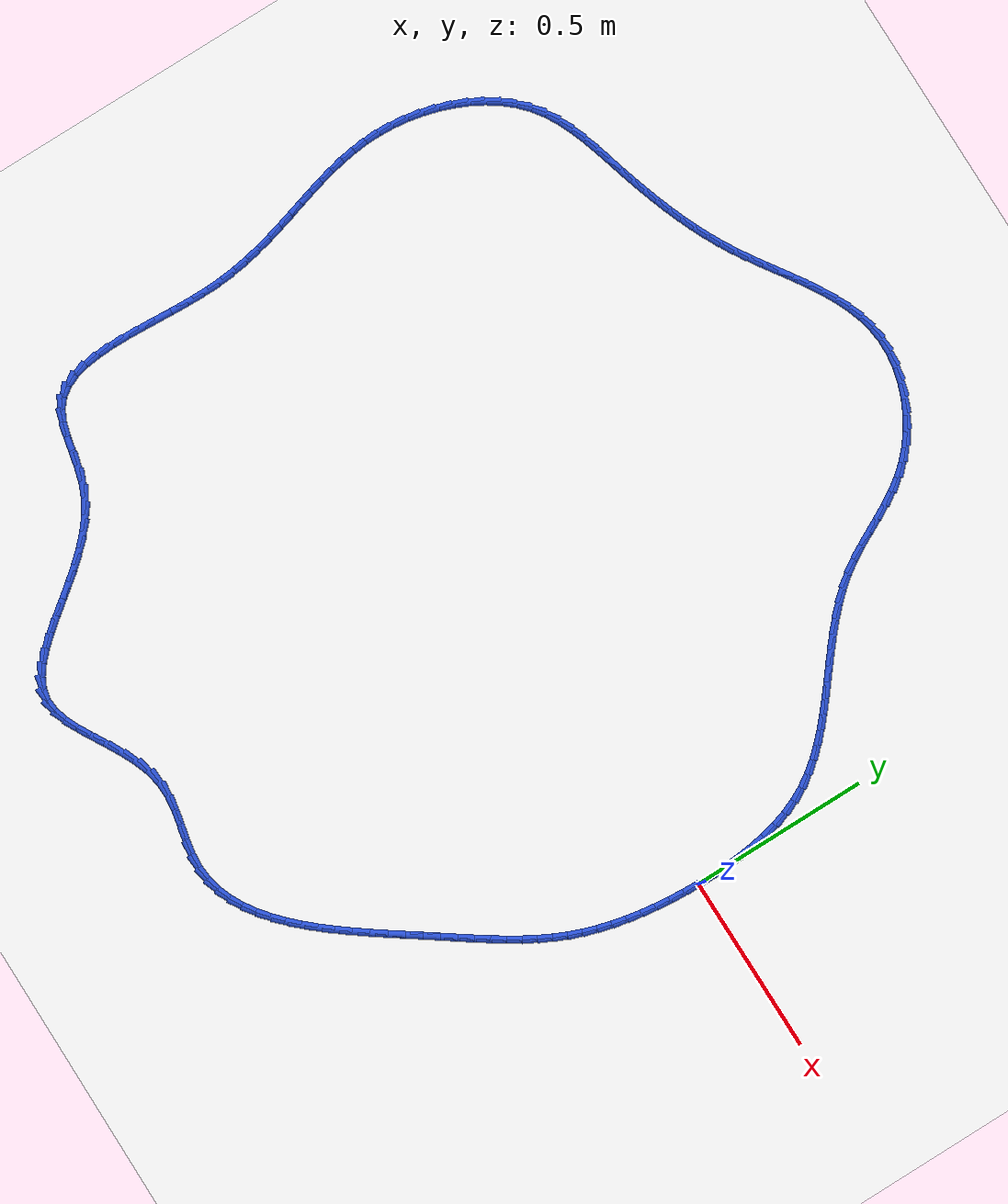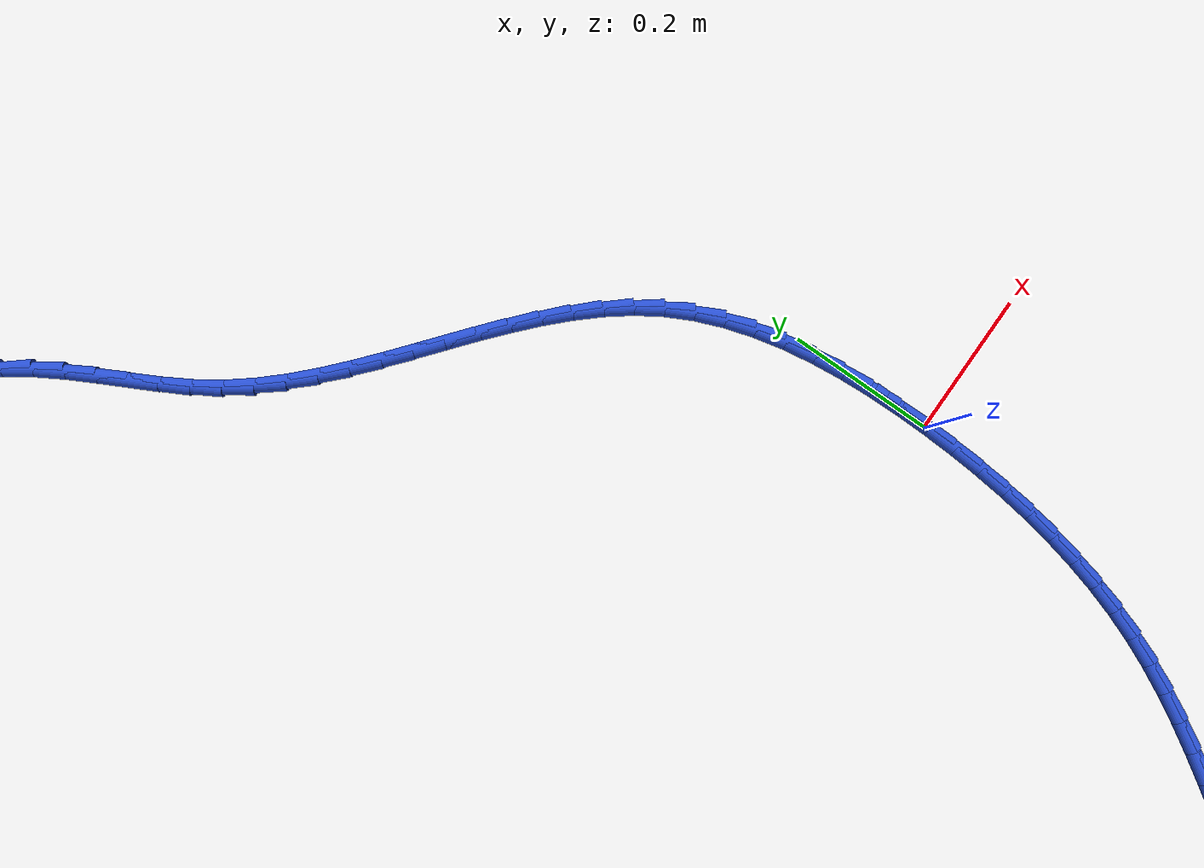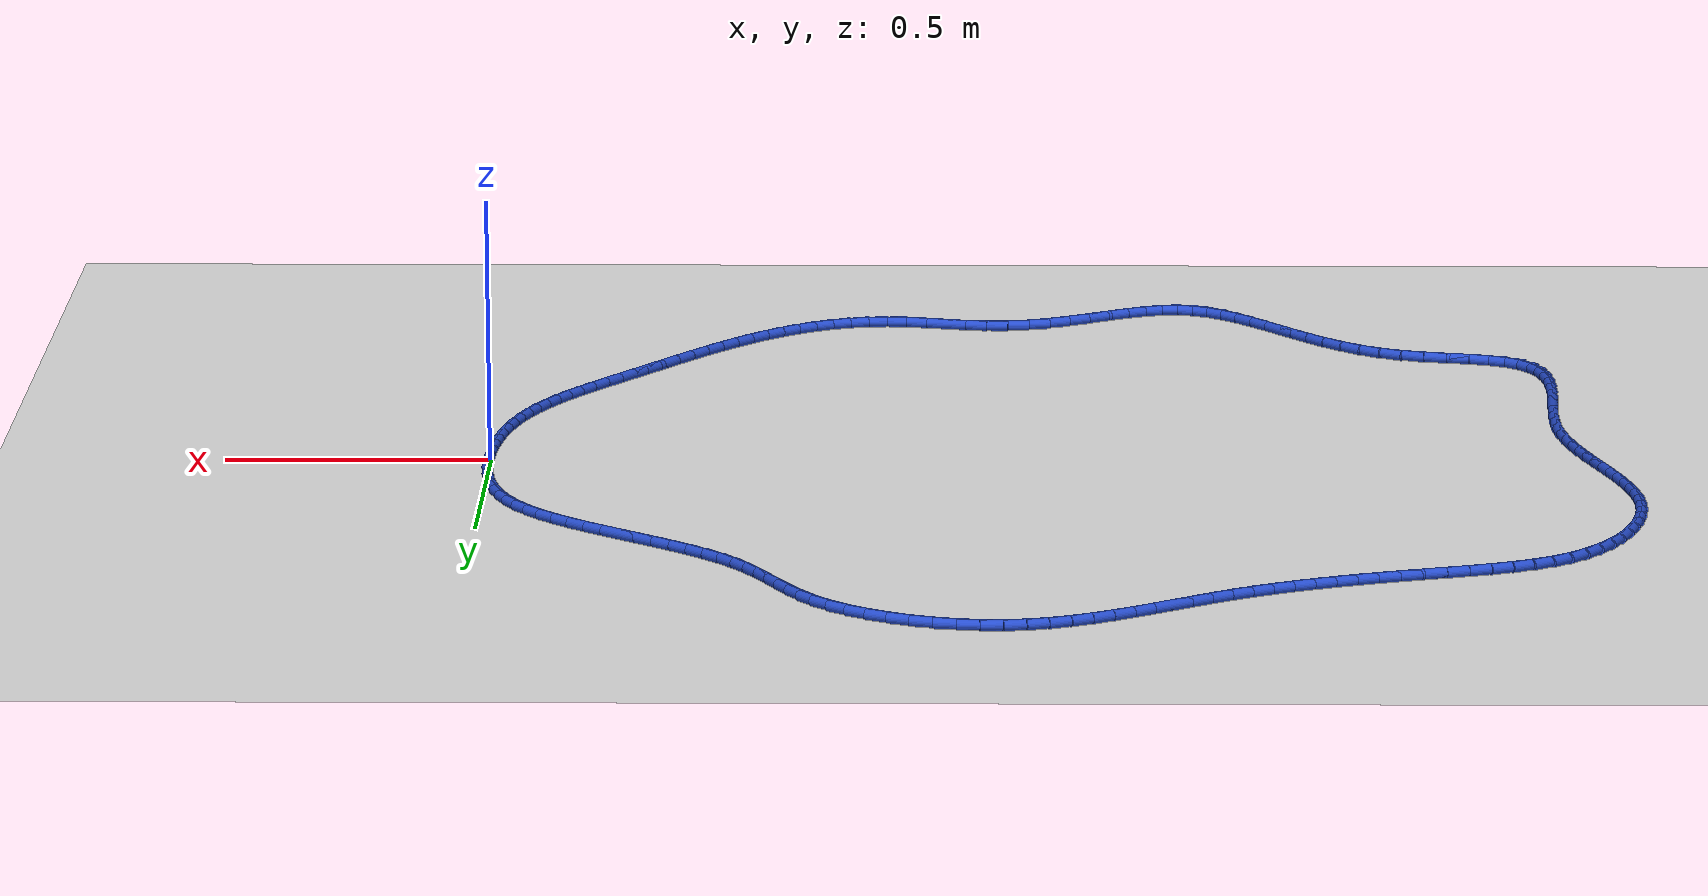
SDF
<sdf version="1.6">
 <world name="default">
  <light name="sun" type="directional">
   <pose>0 0 10 0 -0 0</pose>
   <diffuse>0.8 0.8 0.8 1</diffuse>
   <specular>0.2 0.2 0.2 1</specular>
   <attenuation>
    <range>1000</range>
    <constant>0.9</constant>
    <linear>0.01</linear>
    <quadratic>0.001</quadratic>
   </attenuation>
   <direction>-0.5 0.1 -0.9</direction>
  </light>
  <model name="ground_plane">
   <static>1</static>
   <link name="link">
    <collision name="collision">
     <geometry><plane><normal>0 0 1</normal><size>100 100</size></plane></geometry>
     <surface><friction><ode><mu>100</mu><mu2>50</mu2></ode></friction></surface>
    </collision>
    <visual name="visual">
     <cast_shadows>0</cast_shadows>
     <geometry><plane><normal>0 0 1</normal><size>100 100</size></plane></geometry>
     <material>
      <script><uri>file://media/materials/scripts/gazebo.material</uri><name>Gazebo/WhiteGlow</name></script>
     </material>
    </visual>
   </link>
  </model>
  <gravity>0 0 -9.8</gravity>
  <magnetic_field>6e-06 2.3e-05 -4.2e-05</magnetic_field>
  <atmosphere type="adiabatic"/>
  <physics name="default_physics" default="0" type="ode">
   <max_step_size>0.001</max_step_size>
   <real_time_factor>1</real_time_factor>
   <real_time_update_rate>1000</real_time_update_rate>
  </physics>
  <scene><ambient>0.4 0.4 0.4 1</ambient><background>0.7 0.7 0.7 1</background><shadows>1</shadows></scene>
  <spherical_coordinates>
   <surface_model>EARTH_WGS84</surface_model>
   <latitude_deg>0</latitude_deg>
   <longitude_deg>0</longitude_deg>
   <elevation>0</elevation>
   <heading_deg>0</heading_deg>
  </spherical_coordinates>
  <model name="line">
   <link name="link_0">
    <pose>2.6020852139652106e-18 0.0 0.01 0 1.57 1.5603672017966557</pose>
    <collision name="collision">
     <geometry><cylinder><radius>0.01</radius><length>0.08</length></cylinder></geometry>
    </collision>
    <visual name="visual">
     <material>
      <script><name>Gazebo/Blue</name><uri>file://media/materials/scripts/gazebo.material</uri></script>
     </material>
     <geometry><cylinder><radius>0.01</radius><length>0.08</length></cylinder></geometry>
    </visual>
   </link>
   <link name="link_1">
    <pose>0.00045002174110240323 0.043148914724343616 0.01 0 1.57 -1.5474597674245667</pose>
    <collision name="collision">
     <geometry><cylinder><radius>0.01</radius><length>0.08</length></cylinder></geometry>
    </collision>
    <visual name="visual">
     <material>
      <script><name>Gazebo/Blue</name><uri>file://media/materials/scripts/gazebo.material</uri></script>
     </material>
     <geometry><cylinder><radius>0.01</radius><length>0.08</length></cylinder></geometry>
    </visual>
   </link>
   <link name="link_2">
    <pose>-0.0005565952846127219 0.08627585002966279 0.01 0 1.57 -1.5074508269520739</pose>
    <collision name="collision">
     <geometry><cylinder><radius>0.01</radius><length>0.08</length></cylinder></geometry>
    </collision>
    <visual name="visual">
     <material>
      <script><name>Gazebo/Blue</name><uri>file://media/materials/scripts/gazebo.material</uri></script>
     </material>
     <geometry><cylinder><radius>0.01</radius><length>0.08</length></cylinder></geometry>
    </visual>
   </link>
   <link name="link_3">
    <pose>-0.0032737772847034525 0.1291130944323196 0.01 0 1.57 -1.4605149708257072</pose>
    <collision name="collision">
     <geometry><cylinder><radius>0.01</radius><length>0.08</length></cylinder></geometry>
    </collision>
    <visual name="visual">
     <material>
      <script><name>Gazebo/Blue</name><uri>file://media/materials/scripts/gazebo.material</uri></script>
     </material>
     <geometry><cylinder><radius>0.01</radius><length>0.08</length></cylinder></geometry>
    </visual>
   </link>
   <link name="link_4">
    <pose>-0.007955450466727878 0.17139293644867626 0.01 0 1.57 -1.4058596160627999</pose>
    <collision name="collision">
     <geometry><cylinder><radius>0.01</radius><length>0.08</length></cylinder></geometry>
    </collision>
    <visual name="visual">
     <material>
      <script><name>Gazebo/Blue</name><uri>file://media/materials/scripts/gazebo.material</uri></script>
     </material>
     <geometry><cylinder><radius>0.01</radius><length>0.08</length></cylinder></geometry>
    </visual>
   </link>
   <link name="link_5">
    <pose>-0.014855541038244081 0.21284766459509488 0.01 0 1.57 -1.3426300670088354</pose>
    <collision name="collision">
     <geometry><cylinder><radius>0.01</radius><length>0.08</length></cylinder></geometry>
    </collision>
    <visual name="visual">
     <material>
      <script><name>Gazebo/Blue</name><uri>file://media/materials/scripts/gazebo.material</uri></script>
     </material>
     <geometry><cylinder><radius>0.01</radius><length>0.08</length></cylinder></geometry>
    </visual>
   </link>
   <link name="link_6">
    <pose>-0.02422797520681013 0.25320956738793743 0.01 0 1.57 -1.2699969691177238</pose>
    <collision name="collision">
     <geometry><cylinder><radius>0.01</radius><length>0.08</length></cylinder></geometry>
    </collision>
    <visual name="visual">
     <material>
      <script><name>Gazebo/Blue</name><uri>file://media/materials/scripts/gazebo.material</uri></script>
     </material>
     <geometry><cylinder><radius>0.01</radius><length>0.08</length></cylinder></geometry>
    </visual>
   </link>
   <link name="link_7">
    <pose>-0.036326679179984125 0.2922109333435662 0.01 0 1.57 -1.1873028857783643</pose>
    <collision name="collision">
     <geometry><cylinder><radius>0.01</radius><length>0.08</length></cylinder></geometry>
    </collision>
    <visual name="visual">
     <material>
      <script><name>Gazebo/Blue</name><uri>file://media/materials/scripts/gazebo.material</uri></script>
     </material>
     <geometry><cylinder><radius>0.01</radius><length>0.08</length></cylinder></geometry>
    </visual>
   </link>
   <link name="link_8">
    <pose>-0.051405579165324136 0.3295840509783432 0.01 0 1.57 -1.0942841583224854</pose>
    <collision name="collision">
     <geometry><cylinder><radius>0.01</radius><length>0.08</length></cylinder></geometry>
    </collision>
    <visual name="visual">
     <material>
      <script><name>Gazebo/Blue</name><uri>file://media/materials/scripts/gazebo.material</uri></script>
     </material>
     <geometry><cylinder><radius>0.01</radius><length>0.08</length></cylinder></geometry>
    </visual>
   </link>
   <link name="link_9">
    <pose>-0.0697184450380698 0.3650613332019651 0.01 0 1.57 -0.996380245673062</pose>
    <collision name="collision">
     <geometry><cylinder><radius>0.01</radius><length>0.08</length></cylinder></geometry>
    </collision>
    <visual name="visual">
     <material>
      <script><name>Gazebo/Blue</name><uri>file://media/materials/scripts/gazebo.material</uri></script>
     </material>
     <geometry><cylinder><radius>0.01</radius><length>0.08</length></cylinder></geometry>
    </visual>
   </link>
   <link name="link_10">
    <pose>-0.0913610808833518 0.3985008860088433 0.01 0 1.57 -0.9093972416215466</pose>
    <collision name="collision">
     <geometry><cylinder><radius>0.01</radius><length>0.08</length></cylinder></geometry>
    </collision>
    <visual name="visual">
     <material>
      <script><name>Gazebo/Blue</name><uri>file://media/materials/scripts/gazebo.material</uri></script>
     </material>
     <geometry><cylinder><radius>0.01</radius><length>0.08</length></cylinder></geometry>
    </visual>
   </link>
   <link name="link_11">
    <pose>-0.11597412124693667 0.4301229929473489 0.01 0 1.57 -0.8368479725677014</pose>
    <collision name="collision">
     <geometry><cylinder><radius>0.01</radius><length>0.08</length></cylinder></geometry>
    </collision>
    <visual name="visual">
     <material>
      <script><name>Gazebo/Blue</name><uri>file://media/materials/scripts/gazebo.material</uri></script>
     </material>
     <geometry><cylinder><radius>0.01</radius><length>0.08</length></cylinder></geometry>
    </visual>
   </link>
   <link name="link_12">
    <pose>-0.14311671116471883 0.4602127786169489 0.01 0 1.57 -0.7787051415591466</pose>
    <collision name="collision">
     <geometry><cylinder><radius>0.01</radius><length>0.08</length></cylinder></geometry>
    </collision>
    <visual name="visual">
     <material>
      <script><name>Gazebo/Blue</name><uri>file://media/materials/scripts/gazebo.material</uri></script>
     </material>
     <geometry><cylinder><radius>0.01</radius><length>0.08</length></cylinder></geometry>
    </visual>
   </link>
   <link name="link_13">
    <pose>-0.1723479956725925 0.48905536761710977 0.01 0 1.57 -0.7344106457925842</pose>
    <collision name="collision">
     <geometry><cylinder><radius>0.01</radius><length>0.08</length></cylinder></geometry>
    </collision>
    <visual name="visual">
     <material>
      <script><name>Gazebo/Blue</name><uri>file://media/materials/scripts/gazebo.material</uri></script>
     </material>
     <geometry><cylinder><radius>0.01</radius><length>0.08</length></cylinder></geometry>
    </visual>
   </link>
   <link name="link_14">
    <pose>-0.20322711980645197 0.5169358845472981 0.01 0 1.57 -0.7032329872500405</pose>
    <collision name="collision">
     <geometry><cylinder><radius>0.01</radius><length>0.08</length></cylinder></geometry>
    </collision>
    <visual name="visual">
     <material>
      <script><name>Gazebo/Blue</name><uri>file://media/materials/scripts/gazebo.material</uri></script>
     </material>
     <geometry><cylinder><radius>0.01</radius><length>0.08</length></cylinder></geometry>
    </visual>
   </link>
   <link name="link_15">
    <pose>-0.23531322860219148 0.5441394540069803 0.01 0 1.57 -0.6845001135944201</pose>
    <collision name="collision">
     <geometry><cylinder><radius>0.01</radius><length>0.08</length></cylinder></geometry>
    </collision>
    <visual name="visual">
     <material>
      <script><name>Gazebo/Blue</name><uri>file://media/materials/scripts/gazebo.material</uri></script>
     </material>
     <geometry><cylinder><radius>0.01</radius><length>0.08</length></cylinder></geometry>
    </visual>
   </link>
   <link name="link_16">
    <pose>-0.26816546709570555 0.5709512005956237 0.01 0 1.57 -0.6777301723443366</pose>
    <collision name="collision">
     <geometry><cylinder><radius>0.01</radius><length>0.08</length></cylinder></geometry>
    </collision>
    <visual name="visual">
     <material>
      <script><name>Gazebo/Blue</name><uri>file://media/materials/scripts/gazebo.material</uri></script>
     </material>
     <geometry><cylinder><radius>0.01</radius><length>0.08</length></cylinder></geometry>
    </visual>
   </link>
   <link name="link_17">
    <pose>-0.30134298032288837 0.5976562489126944 0.01 0 1.57 -0.6826927351109306</pose>
    <collision name="collision">
     <geometry><cylinder><radius>0.01</radius><length>0.08</length></cylinder></geometry>
    </collision>
    <visual name="visual">
     <material>
      <script><name>Gazebo/Blue</name><uri>file://media/materials/scripts/gazebo.material</uri></script>
     </material>
     <geometry><cylinder><radius>0.01</radius><length>0.08</length></cylinder></geometry>
    </visual>
   </link>
   <link name="link_18">
    <pose>-0.3344049133196341 0.6245397235576591 0.01 0 1.57 -0.6994242389969801</pose>
    <collision name="collision">
     <geometry><cylinder><radius>0.01</radius><length>0.08</length></cylinder></geometry>
    </collision>
    <visual name="visual">
     <material>
      <script><name>Gazebo/Blue</name><uri>file://media/materials/scripts/gazebo.material</uri></script>
     </material>
     <geometry><cylinder><radius>0.01</radius><length>0.08</length></cylinder></geometry>
    </visual>
   </link>
   <link name="link_19">
    <pose>-0.3669104111218373 0.6518867491299845 0.01 0 1.57 -0.7282075311288307</pose>
    <collision name="collision">
     <geometry><cylinder><radius>0.01</radius><length>0.08</length></cylinder></geometry>
    </collision>
    <visual name="visual">
     <material>
      <script><name>Gazebo/Blue</name><uri>file://media/materials/scripts/gazebo.material</uri></script>
     </material>
     <geometry><cylinder><radius>0.01</radius><length>0.08</length></cylinder></geometry>
    </visual>
   </link>
   <link name="link_20">
    <pose>-0.3984186187653921 0.6799824502291371 0.01 0 1.57 -0.769511523250999</pose>
    <collision name="collision">
     <geometry><cylinder><radius>0.01</radius><length>0.08</length></cylinder></geometry>
    </collision>
    <visual name="visual">
     <material>
      <script><name>Gazebo/Blue</name><uri>file://media/materials/scripts/gazebo.material</uri></script>
     </material>
     <geometry><cylinder><radius>0.01</radius><length>0.08</length></cylinder></geometry>
    </visual>
   </link>
   <link name="link_21">
    <pose>-0.4284886812861927 0.7091119514545836 0.01 0 1.57 -0.8238747855138431</pose>
    <collision name="collision">
     <geometry><cylinder><radius>0.01</radius><length>0.08</length></cylinder></geometry>
    </collision>
    <visual name="visual">
     <material>
      <script><name>Gazebo/Blue</name><uri>file://media/materials/scripts/gazebo.material</uri></script>
     </material>
     <geometry><cylinder><radius>0.01</radius><length>0.08</length></cylinder></geometry>
    </visual>
   </link>
   <link name="link_22">
    <pose>-0.4566797437201335 0.7395603774057905 0.01 0 1.57 -0.8917098272765633</pose>
    <collision name="collision">
     <geometry><cylinder><radius>0.01</radius><length>0.08</length></cylinder></geometry>
    </collision>
    <visual name="visual">
     <material>
      <script><name>Gazebo/Blue</name><uri>file://media/materials/scripts/gazebo.material</uri></script>
     </material>
     <geometry><cylinder><radius>0.01</radius><length>0.08</length></cylinder></geometry>
    </visual>
   </link>
   <link name="link_23">
    <pose>-0.4825509511031091 0.7716128526822251 0.01 0 1.57 -0.9713835721225375</pose>
    <collision name="collision">
     <geometry><cylinder><radius>0.01</radius><length>0.08</length></cylinder></geometry>
    </collision>
    <visual name="visual">
     <material>
      <script><name>Gazebo/Blue</name><uri>file://media/materials/scripts/gazebo.material</uri></script>
     </material>
     <geometry><cylinder><radius>0.01</radius><length>0.08</length></cylinder></geometry>
    </visual>
   </link>
   <link name="link_24">
    <pose>-0.5057175224394685 0.8055180439164932 0.01 0 1.57 -1.0397373057597057</pose>
    <collision name="collision">
     <geometry><cylinder><radius>0.01</radius><length>0.08</length></cylinder></geometry>
    </collision>
    <visual name="visual">
     <material>
      <script><name>Gazebo/Blue</name><uri>file://media/materials/scripts/gazebo.material</uri></script>
     </material>
     <geometry><cylinder><radius>0.01</radius><length>0.08</length></cylinder></geometry>
    </visual>
   </link>
   <link name="link_25">
    <pose>-0.5265696846647365 0.8410207259309762 0.01 0 1.57 -1.0800094032478889</pose>
    <collision name="collision">
     <geometry><cylinder><radius>0.01</radius><length>0.08</length></cylinder></geometry>
    </collision>
    <visual name="visual">
     <material>
      <script><name>Gazebo/Blue</name><uri>file://media/materials/scripts/gazebo.material</uri></script>
     </material>
     <geometry><cylinder><radius>0.01</radius><length>0.08</length></cylinder></geometry>
    </visual>
   </link>
   <link name="link_26">
    <pose>-0.5460631289883203 0.8774980220633136 0.01 0 1.57 -1.0922069597904753</pose>
    <collision name="collision">
     <geometry><cylinder><radius>0.01</radius><length>0.08</length></cylinder></geometry>
    </collision>
    <visual name="visual">
     <material>
      <script><name>Gazebo/Blue</name><uri>file://media/materials/scripts/gazebo.material</uri></script>
     </material>
     <geometry><cylinder><radius>0.01</radius><length>0.08</length></cylinder></geometry>
    </visual>
   </link>
   <link name="link_27">
    <pose>-0.565166402060116 0.9143186973480628 0.01 0 1.57 -1.0766400171323605</pose>
    <collision name="collision">
     <geometry><cylinder><radius>0.01</radius><length>0.08</length></cylinder></geometry>
    </collision>
    <visual name="visual">
     <material>
      <script><name>Gazebo/Blue</name><uri>file://media/materials/scripts/gazebo.material</uri></script>
     </material>
     <geometry><cylinder><radius>0.01</radius><length>0.08</length></cylinder></geometry>
    </visual>
   </link>
   <link name="link_28">
    <pose>-0.5848480505300198 0.950851516819782 0.01 0 1.57 -1.0332654261850762</pose>
    <collision name="collision">
     <geometry><cylinder><radius>0.01</radius><length>0.08</length></cylinder></geometry>
    </collision>
    <visual name="visual">
     <material>
      <script><name>Gazebo/Blue</name><uri>file://media/materials/scripts/gazebo.material</uri></script>
     </material>
     <geometry><cylinder><radius>0.01</radius><length>0.08</length></cylinder></geometry>
    </visual>
   </link>
   <link name="link_29">
    <pose>-0.6060766210479278 0.9864652455130287 0.01 0 1.57 -0.9620501244901579</pose>
    <collision name="collision">
     <geometry><cylinder><radius>0.01</radius><length>0.08</length></cylinder></geometry>
    </collision>
    <visual name="visual">
     <material>
      <script><name>Gazebo/Blue</name><uri>file://media/materials/scripts/gazebo.material</uri></script>
     </material>
     <geometry><cylinder><radius>0.01</radius><length>0.08</length></cylinder></geometry>
    </visual>
   </link>
   <link name="link_30">
    <pose>-0.6298206602637358 1.02052864846236 0.01 0 1.57 -0.8641561636152018</pose>
    <collision name="collision">
     <geometry><cylinder><radius>0.01</radius><length>0.08</length></cylinder></geometry>
    </collision>
    <visual name="visual">
     <material>
      <script><name>Gazebo/Blue</name><uri>file://media/materials/scripts/gazebo.material</uri></script>
     </material>
     <geometry><cylinder><radius>0.01</radius><length>0.08</length></cylinder></geometry>
    </visual>
   </link>
   <link name="link_31">
    <pose>-0.6570397124970522 1.0524121476929484 0.01 0 1.57 -0.7540346225117152</pose>
    <collision name="collision">
     <geometry><cylinder><radius>0.01</radius><length>0.08</length></cylinder></geometry>
    </collision>
    <visual name="visual">
     <material>
      <script><name>Gazebo/Blue</name><uri>file://media/materials/scripts/gazebo.material</uri></script>
     </material>
     <geometry><cylinder><radius>0.01</radius><length>0.08</length></cylinder></geometry>
    </visual>
   </link>
   <link name="link_32">
    <pose>-0.6881112286628995 1.0815933067452037 0.01 0 1.57 -0.6499195010057198</pose>
    <collision name="collision">
     <geometry><cylinder><radius>0.01</radius><length>0.08</length></cylinder></geometry>
    </collision>
    <visual name="visual">
     <material>
      <script><name>Gazebo/Blue</name><uri>file://media/materials/scripts/gazebo.material</uri></script>
     </material>
     <geometry><cylinder><radius>0.01</radius><length>0.08</length></cylinder></geometry>
    </visual>
   </link>
   <link name="link_33">
    <pose>-0.7224854272697202 1.1077203577914716 0.01 0 1.57 -0.5504771488180071</pose>
    <collision name="collision">
     <geometry><cylinder><radius>0.01</radius><length>0.08</length></cylinder></geometry>
    </collision>
    <visual name="visual">
     <material>
      <script><name>Gazebo/Blue</name><uri>file://media/materials/scripts/gazebo.material</uri></script>
     </material>
     <geometry><cylinder><radius>0.01</radius><length>0.08</length></cylinder></geometry>
    </visual>
   </link>
   <link name="link_34">
    <pose>-0.759529771194415 1.1304567652051294 0.01 0 1.57 -0.4527037058236821</pose>
    <collision name="collision">
     <geometry><cylinder><radius>0.01</radius><length>0.08</length></cylinder></geometry>
    </collision>
    <visual name="visual">
     <material>
      <script><name>Gazebo/Blue</name><uri>file://media/materials/scripts/gazebo.material</uri></script>
     </material>
     <geometry><cylinder><radius>0.01</radius><length>0.08</length></cylinder></geometry>
    </visual>
   </link>
   <link name="link_35">
    <pose>-0.7986117233138849 1.1494659933595548 0.01 0 1.57 -0.3536261670584787</pose>
    <collision name="collision">
     <geometry><cylinder><radius>0.01</radius><length>0.08</length></cylinder></geometry>
    </collision>
    <visual name="visual">
     <material>
      <script><name>Gazebo/Blue</name><uri>file://media/materials/scripts/gazebo.material</uri></script>
     </material>
     <geometry><cylinder><radius>0.01</radius><length>0.08</length></cylinder></geometry>
    </visual>
   </link>
   <link name="link_36">
    <pose>-0.8390987465050314 1.1644115066281253 0.01 0 1.57 -0.25022679561089617</pose>
    <collision name="collision">
     <geometry><cylinder><radius>0.01</radius><length>0.08</length></cylinder></geometry>
    </collision>
    <visual name="visual">
     <material>
      <script><name>Gazebo/Blue</name><uri>file://media/materials/scripts/gazebo.material</uri></script>
     </material>
     <geometry><cylinder><radius>0.01</radius><length>0.08</length></cylinder></geometry>
    </visual>
   </link>
   <link name="link_37">
    <pose>-0.8803583036447554 1.1749567693842184 0.01 0 1.57 -0.1393929859594131</pose>
    <collision name="collision">
     <geometry><cylinder><radius>0.01</radius><length>0.08</length></cylinder></geometry>
    </collision>
    <visual name="visual">
     <material>
      <script><name>Gazebo/Blue</name><uri>file://media/materials/scripts/gazebo.material</uri></script>
     </material>
     <geometry><cylinder><radius>0.01</radius><length>0.08</length></cylinder></geometry>
    </visual>
   </link>
   <link name="link_38">
    <pose>-0.9217578576099578 1.1807652460012115 0.01 0 1.57 -0.017969430090186148</pose>
    <collision name="collision">
     <geometry><cylinder><radius>0.01</radius><length>0.08</length></cylinder></geometry>
    </collision>
    <visual name="visual">
     <material>
      <script><name>Gazebo/Blue</name><uri>file://media/materials/scripts/gazebo.material</uri></script>
     </material>
     <geometry><cylinder><radius>0.01</radius><length>0.08</length></cylinder></geometry>
    </visual>
   </link>
   <link name="link_39">
    <pose>-0.9626648712775403 1.1815004008524823 0.01 0 1.57 0.11282541030389691</pose>
    <collision name="collision">
     <geometry><cylinder><radius>0.01</radius><length>0.08</length></cylinder></geometry>
    </collision>
    <visual name="visual">
     <material>
      <script><name>Gazebo/Blue</name><uri>file://media/materials/scripts/gazebo.material</uri></script>
     </material>
     <geometry><cylinder><radius>0.01</radius><length>0.08</length></cylinder></geometry>
    </visual>
   </link>
   <link name="link_40">
    <pose>-1.00256579323061 1.176979363034606 0.01 0 1.57 0.2345974822309822</pose>
    <collision name="collision">
     <geometry><cylinder><radius>0.01</radius><length>0.08</length></cylinder></geometry>
    </collision>
    <visual name="visual">
     <material>
      <script><name>Gazebo/Blue</name><uri>file://media/materials/scripts/gazebo.material</uri></script>
     </material>
     <geometry><cylinder><radius>0.01</radius><length>0.08</length></cylinder></geometry>
    </visual>
   </link>
   <link name="link_41">
    <pose>-1.0414613292002413 1.1676834017733715 0.01 0 1.57 0.33901113135099137</pose>
    <collision name="collision">
     <geometry><cylinder><radius>0.01</radius><length>0.08</length></cylinder></geometry>
    </collision>
    <visual name="visual">
     <material>
      <script><name>Gazebo/Blue</name><uri>file://media/materials/scripts/gazebo.material</uri></script>
     </material>
     <geometry><cylinder><radius>0.01</radius><length>0.08</length></cylinder></geometry>
    </visual>
   </link>
   <link name="link_42">
    <pose>-1.079491086505613 1.1542731714893821 0.01 0 1.57 0.42457420445043403</pose>
    <collision name="collision">
     <geometry><cylinder><radius>0.01</radius><length>0.08</length></cylinder></geometry>
    </collision>
    <visual name="visual">
     <material>
      <script><name>Gazebo/Blue</name><uri>file://media/materials/scripts/gazebo.material</uri></script>
     </material>
     <geometry><cylinder><radius>0.01</radius><length>0.08</length></cylinder></geometry>
    </visual>
   </link>
   <link name="link_43">
    <pose>-1.1167946746756232 1.1374093294569938 0.01 0 1.57 0.491533177553739</pose>
    <collision name="collision">
     <geometry><cylinder><radius>0.01</radius><length>0.08</length></cylinder></geometry>
    </collision>
    <visual name="visual">
     <material>
      <script><name>Gazebo/Blue</name><uri>file://media/materials/scripts/gazebo.material</uri></script>
     </material>
     <geometry><cylinder><radius>0.01</radius><length>0.08</length></cylinder></geometry>
    </visual>
   </link>
   <link name="link_44">
    <pose>-1.1535117032391695 1.1177525329505622 0.01 0 1.57 0.5409676290574882</pose>
    <collision name="collision">
     <geometry><cylinder><radius>0.01</radius><length>0.08</length></cylinder></geometry>
    </collision>
    <visual name="visual">
     <material>
      <script><name>Gazebo/Blue</name><uri>file://media/materials/scripts/gazebo.material</uri></script>
     </material>
     <geometry><cylinder><radius>0.01</radius><length>0.08</length></cylinder></geometry>
    </visual>
   </link>
   <link name="link_45">
    <pose>-1.1897817817251504 1.095963439244443 0.01 0 1.57 0.5741230505601602</pose>
    <collision name="collision">
     <geometry><cylinder><radius>0.01</radius><length>0.08</length></cylinder></geometry>
    </collision>
    <visual name="visual">
     <material>
      <script><name>Gazebo/Blue</name><uri>file://media/materials/scripts/gazebo.material</uri></script>
     </material>
     <geometry><cylinder><radius>0.01</radius><length>0.08</length></cylinder></geometry>
    </visual>
   </link>
   <link name="link_46">
    <pose>-1.2257445196624617 1.0727027056129914 0.01 0 1.57 0.5920220072797028</pose>
    <collision name="collision">
     <geometry><cylinder><radius>0.01</radius><length>0.08</length></cylinder></geometry>
    </collision>
    <visual name="visual">
     <material>
      <script><name>Gazebo/Blue</name><uri>file://media/materials/scripts/gazebo.material</uri></script>
     </material>
     <geometry><cylinder><radius>0.01</radius><length>0.08</length></cylinder></geometry>
    </visual>
   </link>
   <link name="link_47">
    <pose>-1.2615395265800036 1.0486309893305636 0.01 0 1.57 0.5952730524551635</pose>
    <collision name="collision">
     <geometry><cylinder><radius>0.01</radius><length>0.08</length></cylinder></geometry>
    </collision>
    <visual name="visual">
     <material>
      <script><name>Gazebo/Blue</name><uri>file://media/materials/scripts/gazebo.material</uri></script>
     </material>
     <geometry><cylinder><radius>0.01</radius><length>0.08</length></cylinder></geometry>
    </visual>
   </link>
   <link name="link_48">
    <pose>-1.2973064120066715 1.0244089476715155 0.01 0 1.57 0.5839937026788297</pose>
    <collision name="collision">
     <geometry><cylinder><radius>0.01</radius><length>0.08</length></cylinder></geometry>
    </collision>
    <visual name="visual">
     <material>
      <script><name>Gazebo/Blue</name><uri>file://media/materials/scripts/gazebo.material</uri></script>
     </material>
     <geometry><cylinder><radius>0.01</radius><length>0.08</length></cylinder></geometry>
    </visual>
   </link>
   <link name="link_49">
    <pose>-1.333184785471364 1.0006972379102024 0.01 0 1.57 0.5577988449191743</pose>
    <collision name="collision">
     <geometry><cylinder><radius>0.01</radius><length>0.08</length></cylinder></geometry>
    </collision>
    <visual name="visual">
     <material>
      <script><name>Gazebo/Blue</name><uri>file://media/materials/scripts/gazebo.material</uri></script>
     </material>
     <geometry><cylinder><radius>0.01</radius><length>0.08</length></cylinder></geometry>
    </visual>
   </link>
   <link name="link_50">
    <pose>-1.3693142563289775 0.9781565161938238 0.01 0 1.57 0.519111660124548</pose>
    <collision name="collision">
     <geometry><cylinder><radius>0.01</radius><length>0.08</length></cylinder></geometry>
    </collision>
    <visual name="visual">
     <material>
      <script><name>Gazebo/Blue</name><uri>file://media/materials/scripts/gazebo.material</uri></script>
     </material>
     <geometry><cylinder><radius>0.01</radius><length>0.08</length></cylinder></geometry>
    </visual>
   </link>
   <link name="link_51">
    <pose>-1.4058120305278754 0.9573023133007899 0.01 0 1.57 0.47975570111447596</pose>
    <collision name="collision">
     <geometry><cylinder><radius>0.01</radius><length>0.08</length></cylinder></geometry>
    </collision>
    <visual name="visual">
     <material>
      <script><name>Gazebo/Blue</name><uri>file://media/materials/scripts/gazebo.material</uri></script>
     </material>
     <geometry><cylinder><radius>0.01</radius><length>0.08</length></cylinder></geometry>
    </visual>
   </link>
   <link name="link_52">
    <pose>-1.4427109681783776 0.9381037823487952 0.01 0 1.57 0.4429788780883179</pose>
    <collision name="collision">
     <geometry><cylinder><radius>0.01</radius><length>0.08</length></cylinder></geometry>
    </collision>
    <visual name="visual">
     <material>
      <script><name>Gazebo/Blue</name><uri>file://media/materials/scripts/gazebo.material</uri></script>
     </material>
     <geometry><cylinder><radius>0.01</radius><length>0.08</length></cylinder></geometry>
    </visual>
   </link>
   <link name="link_53">
    <pose>-1.4800240833235068 0.9204015170852705 0.01 0 1.57 0.4091592773785062</pose>
    <collision name="collision">
     <geometry><cylinder><radius>0.01</radius><length>0.08</length></cylinder></geometry>
    </collision>
    <visual name="visual">
     <material>
      <script><name>Gazebo/Blue</name><uri>file://media/materials/scripts/gazebo.material</uri></script>
     </material>
     <geometry><cylinder><radius>0.01</radius><length>0.08</length></cylinder></geometry>
    </visual>
   </link>
   <link name="link_54">
    <pose>-1.517764390006287 0.9040361112576462 0.01 0 1.57 0.37860261845492205</pose>
    <collision name="collision">
     <geometry><cylinder><radius>0.01</radius><length>0.08</length></cylinder></geometry>
    </collision>
    <visual name="visual">
     <material>
      <script><name>Gazebo/Blue</name><uri>file://media/materials/scripts/gazebo.material</uri></script>
     </material>
     <geometry><cylinder><radius>0.01</radius><length>0.08</length></cylinder></geometry>
    </visual>
   </link>
   <link name="link_55">
    <pose>-1.555944902269741 0.888848158613351 0.01 0 1.57 0.35154071192672415</pose>
    <collision name="collision">
     <geometry><cylinder><radius>0.01</radius><length>0.08</length></cylinder></geometry>
    </collision>
    <visual name="visual">
     <material>
      <script><name>Gazebo/Blue</name><uri>file://media/materials/scripts/gazebo.material</uri></script>
     </material>
     <geometry><cylinder><radius>0.01</radius><length>0.08</length></cylinder></geometry>
    </visual>
   </link>
   <link name="link_56">
    <pose>-1.5945786341568913 0.8746782528998158 0.01 0 1.57 0.3281345281221142</pose>
    <collision name="collision">
     <geometry><cylinder><radius>0.01</radius><length>0.08</length></cylinder></geometry>
    </collision>
    <visual name="visual">
     <material>
      <script><name>Gazebo/Blue</name><uri>file://media/materials/scripts/gazebo.material</uri></script>
     </material>
     <geometry><cylinder><radius>0.01</radius><length>0.08</length></cylinder></geometry>
    </visual>
   </link>
   <link name="link_57">
    <pose>-1.6336785997107617 0.8613669878644705 0.01 0 1.57 0.30848048596203403</pose>
    <collision name="collision">
     <geometry><cylinder><radius>0.01</radius><length>0.08</length></cylinder></geometry>
    </collision>
    <visual name="visual">
     <material>
      <script><name>Gazebo/Blue</name><uri>file://media/materials/scripts/gazebo.material</uri></script>
     </material>
     <geometry><cylinder><radius>0.01</radius><length>0.08</length></cylinder></geometry>
    </visual>
   </link>
   <link name="link_58">
    <pose>-1.6732578129743763 0.848754957254745 0.01 0 1.57 0.29261853093962426</pose>
    <collision name="collision">
     <geometry><cylinder><radius>0.01</radius><length>0.08</length></cylinder></geometry>
    </collision>
    <visual name="visual">
     <material>
      <script><name>Gazebo/Blue</name><uri>file://media/materials/scripts/gazebo.material</uri></script>
     </material>
     <geometry><cylinder><radius>0.01</radius><length>0.08</length></cylinder></geometry>
    </visual>
   </link>
   <link name="link_59">
    <pose>-1.7133292879907558 0.8366827548180692 0.01 0 1.57 0.2820205276368981</pose>
    <collision name="collision">
     <geometry><cylinder><radius>0.01</radius><length>0.08</length></cylinder></geometry>
    </collision>
    <visual name="visual">
     <material>
      <script><name>Gazebo/Blue</name><uri>file://media/materials/scripts/gazebo.material</uri></script>
     </material>
     <geometry><cylinder><radius>0.01</radius><length>0.08</length></cylinder></geometry>
    </visual>
   </link>
   <link name="link_60">
    <pose>-1.7538559603219255 0.8249404270721054 0.01 0 1.57 0.2867878664182833</pose>
    <collision name="collision">
     <geometry><cylinder><radius>0.01</radius><length>0.08</length></cylinder></geometry>
    </collision>
    <visual name="visual">
     <material>
      <script><name>Gazebo/Blue</name><uri>file://media/materials/scripts/gazebo.material</uri></script>
     </material>
     <geometry><cylinder><radius>0.01</radius><length>0.08</length></cylinder></geometry>
    </visual>
   </link>
   <link name="link_61">
    <pose>-1.7944534842075353 0.8129674885605879 0.01 0 1.57 0.31125611164915234</pose>
    <collision name="collision">
     <geometry><cylinder><radius>0.01</radius><length>0.08</length></cylinder></geometry>
    </collision>
    <visual name="visual">
     <material>
      <script><name>Gazebo/Blue</name><uri>file://media/materials/scripts/gazebo.material</uri></script>
     </material>
     <geometry><cylinder><radius>0.01</radius><length>0.08</length></cylinder></geometry>
    </visual>
   </link>
   <link name="link_62">
    <pose>-1.8345903665537737 0.8000549291530666 0.01 0 1.57 0.3561396616481073</pose>
    <collision name="collision">
     <geometry><cylinder><radius>0.01</radius><length>0.08</length></cylinder></geometry>
    </collision>
    <visual name="visual">
     <material>
      <script><name>Gazebo/Blue</name><uri>file://media/materials/scripts/gazebo.material</uri></script>
     </material>
     <geometry><cylinder><radius>0.01</radius><length>0.08</length></cylinder></geometry>
    </visual>
   </link>
   <link name="link_63">
    <pose>-1.873734584127282 0.7854932036172853 0.01 0 1.57 0.42266929820918164</pose>
    <collision name="collision">
     <geometry><cylinder><radius>0.01</radius><length>0.08</length></cylinder></geometry>
    </collision>
    <visual name="visual">
     <material>
      <script><name>Gazebo/Blue</name><uri>file://media/materials/scripts/gazebo.material</uri></script>
     </material>
     <geometry><cylinder><radius>0.01</radius><length>0.08</length></cylinder></geometry>
    </visual>
   </link>
   <link name="link_64">
    <pose>-1.9113541136947 0.7685727667209888 0.01 0 1.57 0.5120606206509861</pose>
    <collision name="collision">
     <geometry><cylinder><radius>0.01</radius><length>0.08</length></cylinder></geometry>
    </collision>
    <visual name="visual">
     <material>
      <script><name>Gazebo/Blue</name><uri>file://media/materials/scripts/gazebo.material</uri></script>
     </material>
     <geometry><cylinder><radius>0.01</radius><length>0.08</length></cylinder></geometry>
    </visual>
   </link>
   <link name="link_65">
    <pose>-1.9469169320226682 0.7485840732319211 0.01 0 1.57 0.624495679351274</pose>
    <collision name="collision">
     <geometry><cylinder><radius>0.01</radius><length>0.08</length></cylinder></geometry>
    </collision>
    <visual name="visual">
     <material>
      <script><name>Gazebo/Blue</name><uri>file://media/materials/scripts/gazebo.material</uri></script>
     </material>
     <geometry><cylinder><radius>0.01</radius><length>0.08</length></cylinder></geometry>
    </visual>
   </link>
   <link name="link_66">
    <pose>-1.9798914871786766 0.7248187217383987 0.01 0 1.57 0.7495319818036402</pose>
    <collision name="collision">
     <geometry><cylinder><radius>0.01</radius><length>0.08</length></cylinder></geometry>
    </collision>
    <visual name="visual">
     <material>
      <script><name>Gazebo/Blue</name><uri>file://media/materials/scripts/gazebo.material</uri></script>
     </material>
     <geometry><cylinder><radius>0.01</radius><length>0.08</length></cylinder></geometry>
    </visual>
   </link>
   <link name="link_67">
    <pose>-2.0098843971127023 0.6969036413393274 0.01 0 1.57 0.8652902120515885</pose>
    <collision name="collision">
     <geometry><cylinder><radius>0.01</radius><length>0.08</length></cylinder></geometry>
    </collision>
    <visual name="visual">
     <material>
      <script><name>Gazebo/Blue</name><uri>file://media/materials/scripts/gazebo.material</uri></script>
     </material>
     <geometry><cylinder><radius>0.01</radius><length>0.08</length></cylinder></geometry>
    </visual>
   </link>
   <link name="link_68">
    <pose>-2.0368318744263165 0.6652656687604622 0.01 0 1.57 0.9694951954688829</pose>
    <collision name="collision">
     <geometry><cylinder><radius>0.01</radius><length>0.08</length></cylinder></geometry>
    </collision>
    <visual name="visual">
     <material>
      <script><name>Gazebo/Blue</name><uri>file://media/materials/scripts/gazebo.material</uri></script>
     </material>
     <geometry><cylinder><radius>0.01</radius><length>0.08</length></cylinder></geometry>
    </visual>
   </link>
   <link name="link_69">
    <pose>-2.060718231027224 0.6304483750302506 0.01 0 1.57 1.0636508722380829</pose>
    <collision name="collision">
     <geometry><cylinder><radius>0.01</radius><length>0.08</length></cylinder></geometry>
    </collision>
    <visual name="visual">
     <material>
      <script><name>Gazebo/Blue</name><uri>file://media/materials/scripts/gazebo.material</uri></script>
     </material>
     <geometry><cylinder><radius>0.01</radius><length>0.08</length></cylinder></geometry>
    </visual>
   </link>
   <link name="link_70">
    <pose>-2.08152777882313 0.5929953311771392 0.01 0 1.57 1.1495901873647019</pose>
    <collision name="collision">
     <geometry><cylinder><radius>0.01</radius><length>0.08</length></cylinder></geometry>
    </collision>
    <visual name="visual">
     <material>
      <script><name>Gazebo/Blue</name><uri>file://media/materials/scripts/gazebo.material</uri></script>
     </material>
     <geometry><cylinder><radius>0.01</radius><length>0.08</length></cylinder></geometry>
    </visual>
   </link>
   <link name="link_71">
    <pose>-2.0992448297217403 0.5534501082295749 0.01 0 1.57 1.229229963399816</pose>
    <collision name="collision">
     <geometry><cylinder><radius>0.01</radius><length>0.08</length></cylinder></geometry>
    </collision>
    <visual name="visual">
     <material>
      <script><name>Gazebo/Blue</name><uri>file://media/materials/scripts/gazebo.material</uri></script>
     </material>
     <geometry><cylinder><radius>0.01</radius><length>0.08</length></cylinder></geometry>
    </visual>
   </link>
   <link name="link_72">
    <pose>-2.1138536956307603 0.5123562772160049 0.01 0 1.57 1.3044672652421363</pose>
    <collision name="collision">
     <geometry><cylinder><radius>0.01</radius><length>0.08</length></cylinder></geometry>
    </collision>
    <visual name="visual">
     <material>
      <script><name>Gazebo/Blue</name><uri>file://media/materials/scripts/gazebo.material</uri></script>
     </material>
     <geometry><cylinder><radius>0.01</radius><length>0.08</length></cylinder></geometry>
    </visual>
   </link>
   <link name="link_73">
    <pose>-2.1253386884578953 0.470257409164876 0.01 0 1.57 1.3771682676088417</pose>
    <collision name="collision">
     <geometry><cylinder><radius>0.01</radius><length>0.08</length></cylinder></geometry>
    </collision>
    <visual name="visual">
     <material>
      <script><name>Gazebo/Blue</name><uri>file://media/materials/scripts/gazebo.material</uri></script>
     </material>
     <geometry><cylinder><radius>0.01</radius><length>0.08</length></cylinder></geometry>
    </visual>
   </link>
   <link name="link_74">
    <pose>-2.13368412011085 0.4276970751046347 0.01 0 1.57 1.4492144426421163</pose>
    <collision name="collision">
     <geometry><cylinder><radius>0.01</radius><length>0.08</length></cylinder></geometry>
    </collision>
    <visual name="visual">
     <material>
      <script><name>Gazebo/Blue</name><uri>file://media/materials/scripts/gazebo.material</uri></script>
     </material>
     <geometry><cylinder><radius>0.01</radius><length>0.08</length></cylinder></geometry>
    </visual>
   </link>
   <link name="link_75">
    <pose>-2.1388743024973307 0.38521884606372886 0.01 0 1.57 1.5225852887236422</pose>
    <collision name="collision">
     <geometry><cylinder><radius>0.01</radius><length>0.08</length></cylinder></geometry>
    </collision>
    <visual name="visual">
     <material>
      <script><name>Gazebo/Blue</name><uri>file://media/materials/scripts/gazebo.material</uri></script>
     </material>
     <geometry><cylinder><radius>0.01</radius><length>0.08</length></cylinder></geometry>
    </visual>
   </link>
   <link name="link_76">
    <pose>-2.1408936291857135 0.3433661497353158 0.01 0 1.57 -1.5445652107656922</pose>
    <collision name="collision">
     <geometry><cylinder><radius>0.01</radius><length>0.08</length></cylinder></geometry>
    </collision>
    <visual name="visual">
     <material>
      <script><name>Gazebo/Blue</name><uri>file://media/materials/scripts/gazebo.material</uri></script>
     </material>
     <geometry><cylinder><radius>0.01</radius><length>0.08</length></cylinder></geometry>
    </visual>
   </link>
   <link name="link_77">
    <pose>-2.1398218147508596 0.3025151011531618 0.01 0 1.57 -1.4758963082030871</pose>
    <collision name="collision">
     <geometry><cylinder><radius>0.01</radius><length>0.08</length></cylinder></geometry>
    </collision>
    <visual name="visual">
     <material>
      <script><name>Gazebo/Blue</name><uri>file://media/materials/scripts/gazebo.material</uri></script>
     </material>
     <geometry><cylinder><radius>0.01</radius><length>0.08</length></cylinder></geometry>
    </visual>
   </link>
   <link name="link_78">
    <pose>-2.1360178523482682 0.2625516102665503 0.01 0 1.57 -1.416076942888644</pose>
    <collision name="collision">
     <geometry><cylinder><radius>0.01</radius><length>0.08</length></cylinder></geometry>
    </collision>
    <visual name="visual">
     <material>
      <script><name>Gazebo/Blue</name><uri>file://media/materials/scripts/gazebo.material</uri></script>
     </material>
     <geometry><cylinder><radius>0.01</radius><length>0.08</length></cylinder></geometry>
    </visual>
   </link>
   <link name="link_79">
    <pose>-2.1298916164983717 0.22327227726194449 0.01 0 1.57 -1.3664979981574357</pose>
    <collision name="collision">
     <geometry><cylinder><radius>0.01</radius><length>0.08</length></cylinder></geometry>
    </collision>
    <visual name="visual">
     <material>
      <script><name>Gazebo/Blue</name><uri>file://media/materials/scripts/gazebo.material</uri></script>
     </material>
     <geometry><cylinder><radius>0.01</radius><length>0.08</length></cylinder></geometry>
    </visual>
   </link>
   <link name="link_80">
    <pose>-2.1218529817216023 0.18447370232580967 0.01 0 1.57 -1.3279968975760823</pose>
    <collision name="collision">
     <geometry><cylinder><radius>0.01</radius><length>0.08</length></cylinder></geometry>
    </collision>
    <visual name="visual">
     <material>
      <script><name>Gazebo/Blue</name><uri>file://media/materials/scripts/gazebo.material</uri></script>
     </material>
     <geometry><cylinder><radius>0.01</radius><length>0.08</length></cylinder></geometry>
    </visual>
   </link>
   <link name="link_81">
    <pose>-2.1123118225383952 0.14595248564460978 0.01 0 1.57 -1.3009601926920586</pose>
    <collision name="collision">
     <geometry><cylinder><radius>0.01</radius><length>0.08</length></cylinder></geometry>
    </collision>
    <visual name="visual">
     <material>
      <script><name>Gazebo/Blue</name><uri>file://media/materials/scripts/gazebo.material</uri></script>
     </material>
     <geometry><cylinder><radius>0.01</radius><length>0.08</length></cylinder></geometry>
    </visual>
   </link>
   <link name="link_82">
    <pose>-2.1016780134691846 0.10750522740480879 0.01 0 1.57 -1.2854489444095845</pose>
    <collision name="collision">
     <geometry><cylinder><radius>0.01</radius><length>0.08</length></cylinder></geometry>
    </collision>
    <visual name="visual">
     <material>
      <script><name>Gazebo/Blue</name><uri>file://media/materials/scripts/gazebo.material</uri></script>
     </material>
     <geometry><cylinder><radius>0.01</radius><length>0.08</length></cylinder></geometry>
    </visual>
   </link>
   <link name="link_83">
    <pose>-2.090361429034402 0.06892852779287176 0.01 0 1.57 -1.2813065990793016</pose>
    <collision name="collision">
     <geometry><cylinder><radius>0.01</radius><length>0.08</length></cylinder></geometry>
    </collision>
    <visual name="visual">
     <material>
      <script><name>Gazebo/Blue</name><uri>file://media/materials/scripts/gazebo.material</uri></script>
     </material>
     <geometry><cylinder><radius>0.01</radius><length>0.08</length></cylinder></geometry>
    </visual>
   </link>
   <link name="link_84">
    <pose>-2.0787719437544814 0.030018986995262197 0.01 0 1.57 -1.2882294400396006</pose>
    <collision name="collision">
     <geometry><cylinder><radius>0.01</radius><length>0.08</length></cylinder></geometry>
    </collision>
    <visual name="visual">
     <material>
      <script><name>Gazebo/Blue</name><uri>file://media/materials/scripts/gazebo.material</uri></script>
     </material>
     <geometry><cylinder><radius>0.01</radius><length>0.08</length></cylinder></geometry>
    </visual>
   </link>
   <link name="link_85">
    <pose>-2.067319432149856 -0.009426794801554797 0.01 0 1.57 -1.3057953818355004</pose>
    <collision name="collision">
     <geometry><cylinder><radius>0.01</radius><length>0.08</length></cylinder></geometry>
    </collision>
    <visual name="visual">
     <material>
      <script><name>Gazebo/Blue</name><uri>file://media/materials/scripts/gazebo.material</uri></script>
     </material>
     <geometry><cylinder><radius>0.01</radius><length>0.08</length></cylinder></geometry>
    </visual>
   </link>
   <link name="link_86">
    <pose>-2.0564137687409603 -0.04961221741111521 0.01 0 1.57 -1.3334563957776255</pose>
    <collision name="collision">
     <geometry><cylinder><radius>0.01</radius><length>0.08</length></cylinder></geometry>
    </collision>
    <visual name="visual">
     <material>
      <script><name>Gazebo/Blue</name><uri>file://media/materials/scripts/gazebo.material</uri></script>
     </material>
     <geometry><cylinder><radius>0.01</radius><length>0.08</length></cylinder></geometry>
    </visual>
   </link>
   <link name="link_87">
    <pose>-2.0464648280482263 -0.09074068064695479 0.01 0 1.57 -1.370505600045153</pose>
    <collision name="collision">
     <geometry><cylinder><radius>0.01</radius><length>0.08</length></cylinder></geometry>
    </collision>
    <visual name="visual">
     <material>
      <script><name>Gazebo/Blue</name><uri>file://media/materials/scripts/gazebo.material</uri></script>
     </material>
     <geometry><cylinder><radius>0.01</radius><length>0.08</length></cylinder></geometry>
    </visual>
   </link>
   <link name="link_88">
    <pose>-2.037882484592088 -0.13301558432260915 0.01 0 1.57 -1.4160344242396123</pose>
    <collision name="collision">
     <geometry><cylinder><radius>0.01</radius><length>0.08</length></cylinder></geometry>
    </collision>
    <visual name="visual">
     <material>
      <script><name>Gazebo/Blue</name><uri>file://media/materials/scripts/gazebo.material</uri></script>
     </material>
     <geometry><cylinder><radius>0.01</radius><length>0.08</length></cylinder></geometry>
    </visual>
   </link>
   <link name="link_89">
    <pose>-2.031076612892979 -0.17664032825161485 0.01 0 1.57 -1.4688987743245947</pose>
    <collision name="collision">
     <geometry><cylinder><radius>0.01</radius><length>0.08</length></cylinder></geometry>
    </collision>
    <visual name="visual">
     <material>
      <script><name>Gazebo/Blue</name><uri>file://media/materials/scripts/gazebo.material</uri></script>
     </material>
     <geometry><cylinder><radius>0.01</radius><length>0.08</length></cylinder></geometry>
    </visual>
   </link>
   <link name="link_90">
    <pose>-2.0264570874713326 -0.22181831224750592 0.01 0 1.57 -1.5270467110702979</pose>
    <collision name="collision">
     <geometry><cylinder><radius>0.01</radius><length>0.08</length></cylinder></geometry>
    </collision>
    <visual name="visual">
     <material>
      <script><name>Gazebo/Blue</name><uri>file://media/materials/scripts/gazebo.material</uri></script>
     </material>
     <geometry><cylinder><radius>0.01</radius><length>0.08</length></cylinder></geometry>
    </visual>
   </link>
   <link name="link_91">
    <pose>-2.0244033698392276 -0.26873088826146374 0.01 0 1.57 1.564706032078261</pose>
    <collision name="collision">
     <geometry><cylinder><radius>0.01</radius><length>0.08</length></cylinder></geometry>
    </collision>
    <visual name="visual">
     <material>
      <script><name>Gazebo/Blue</name><uri>file://media/materials/scripts/gazebo.material</uri></script>
     </material>
     <geometry><cylinder><radius>0.01</radius><length>0.08</length></cylinder></geometry>
    </visual>
   </link>
   <link name="link_92">
    <pose>-2.024698118586612 -0.31712675690919945 0.01 0 1.57 1.5326067948721551</pose>
    <collision name="collision">
     <geometry><cylinder><radius>0.01</radius><length>0.08</length></cylinder></geometry>
    </collision>
    <visual name="visual">
     <material>
      <script><name>Gazebo/Blue</name><uri>file://media/materials/scripts/gazebo.material</uri></script>
     </material>
     <geometry><cylinder><radius>0.01</radius><length>0.08</length></cylinder></geometry>
    </visual>
   </link>
   <link name="link_93">
    <pose>-2.0265792155977302 -0.3663596837943531 0.01 0 1.57 1.5165006969916244</pose>
    <collision name="collision">
     <geometry><cylinder><radius>0.01</radius><length>0.08</length></cylinder></geometry>
    </collision>
    <visual name="visual">
     <material>
      <script><name>Gazebo/Blue</name><uri>file://media/materials/scripts/gazebo.material</uri></script>
     </material>
     <geometry><cylinder><radius>0.01</radius><length>0.08</length></cylinder></geometry>
    </visual>
   </link>
   <link name="link_94">
    <pose>-2.0292645621359133 -0.41576894960100336 0.01 0 1.57 1.5155128352202687</pose>
    <collision name="collision">
     <geometry><cylinder><radius>0.01</radius><length>0.08</length></cylinder></geometry>
    </collision>
    <visual name="visual">
     <material>
      <script><name>Gazebo/Blue</name><uri>file://media/materials/scripts/gazebo.material</uri></script>
     </material>
     <geometry><cylinder><radius>0.01</radius><length>0.08</length></cylinder></geometry>
    </visual>
   </link>
   <link name="link_95">
    <pose>-2.0319720594644908 -0.46469383501322586 0.01 0 1.57 1.5300579300199593</pose>
    <collision name="collision">
     <geometry><cylinder><radius>0.01</radius><length>0.08</length></cylinder></geometry>
    </collision>
    <visual name="visual">
     <material>
      <script><name>Gazebo/Blue</name><uri>file://media/materials/scripts/gazebo.material</uri></script>
     </material>
     <geometry><cylinder><radius>0.01</radius><length>0.08</length></cylinder></geometry>
    </visual>
   </link>
   <link name="link_96">
    <pose>-2.0339196088467943 -0.5124736207150993 0.01 0 1.57 1.5619762876831162</pose>
    <collision name="collision">
     <geometry><cylinder><radius>0.01</radius><length>0.08</length></cylinder></geometry>
    </collision>
    <visual name="visual">
     <material>
      <script><name>Gazebo/Blue</name><uri>file://media/materials/scripts/gazebo.material</uri></script>
     </material>
     <geometry><cylinder><radius>0.01</radius><length>0.08</length></cylinder></geometry>
    </visual>
   </link>
   <link name="link_97">
    <pose>-2.034325111546154 -0.558447587390701 0.01 0 1.57 -1.5267256820878632</pose>
    <collision name="collision">
     <geometry><cylinder><radius>0.01</radius><length>0.08</length></cylinder></geometry>
    </collision>
    <visual name="visual">
     <material>
      <script><name>Gazebo/Blue</name><uri>file://media/materials/scripts/gazebo.material</uri></script>
     </material>
     <geometry><cylinder><radius>0.01</radius><length>0.08</length></cylinder></geometry>
    </visual>
   </link>
   <link name="link_98">
    <pose>-2.0324064688259003 -0.6019550157241085 0.01 0 1.57 -1.4469932806529213</pose>
    <collision name="collision">
     <geometry><cylinder><radius>0.01</radius><length>0.08</length></cylinder></geometry>
    </collision>
    <visual name="visual">
     <material>
      <script><name>Gazebo/Blue</name><uri>file://media/materials/scripts/gazebo.material</uri></script>
     </material>
     <geometry><cylinder><radius>0.01</radius><length>0.08</length></cylinder></geometry>
    </visual>
   </link>
   <link name="link_99">
    <pose>-2.0273815819493635 -0.6423351863994003 0.01 0 1.57 -1.3318664210280116</pose>
    <collision name="collision">
     <geometry><cylinder><radius>0.01</radius><length>0.08</length></cylinder></geometry>
    </collision>
    <visual name="visual">
     <material>
      <script><name>Gazebo/Blue</name><uri>file://media/materials/scripts/gazebo.material</uri></script>
     </material>
     <geometry><cylinder><radius>0.01</radius><length>0.08</length></cylinder></geometry>
    </visual>
   </link>
   <link name="link_100">
    <pose>-2.0184683521798745 -0.6789273801006523 0.01 0 1.57 -1.1709647593265975</pose>
    <collision name="collision">
     <geometry><cylinder><radius>0.01</radius><length>0.08</length></cylinder></geometry>
    </collision>
    <visual name="visual">
     <material>
      <script><name>Gazebo/Blue</name><uri>file://media/materials/scripts/gazebo.material</uri></script>
     </material>
     <geometry><cylinder><radius>0.01</radius><length>0.08</length></cylinder></geometry>
    </visual>
   </link>
   <link name="link_101">
    <pose>-2.004884680780764 -0.7110708775119431 0.01 0 1.57 -0.9572865220179037</pose>
    <collision name="collision">
     <geometry><cylinder><radius>0.01</radius><length>0.08</length></cylinder></geometry>
    </collision>
    <visual name="visual">
     <material>
      <script><name>Gazebo/Blue</name><uri>file://media/materials/scripts/gazebo.material</uri></script>
     </material>
     <geometry><cylinder><radius>0.01</radius><length>0.08</length></cylinder></geometry>
    </visual>
   </link>
   <link name="link_102">
    <pose>-1.985848469015362 -0.7381049593173499 0.01 0 1.57 -0.6995044799015107</pose>
    <collision name="collision">
     <geometry><cylinder><radius>0.01</radius><length>0.08</length></cylinder></geometry>
    </collision>
    <visual name="visual">
     <material>
      <script><name>Gazebo/Blue</name><uri>file://media/materials/scripts/gazebo.material</uri></script>
     </material>
     <geometry><cylinder><radius>0.01</radius><length>0.08</length></cylinder></geometry>
    </visual>
   </link>
   <link name="link_103">
    <pose>-1.9605776181469998 -0.7593689062009504 0.01 0 1.57 -0.444336783079617</pose>
    <collision name="collision">
     <geometry><cylinder><radius>0.01</radius><length>0.08</length></cylinder></geometry>
    </collision>
    <visual name="visual">
     <material>
      <script><name>Gazebo/Blue</name><uri>file://media/materials/scripts/gazebo.material</uri></script>
     </material>
     <geometry><cylinder><radius>0.01</radius><length>0.08</length></cylinder></geometry>
    </visual>
   </link>
   <link name="link_104">
    <pose>-1.928617319520116 -0.7745848643978822 0.01 0 1.57 -0.28346201786628045</pose>
    <collision name="collision">
     <geometry><cylinder><radius>0.01</radius><length>0.08</length></cylinder></geometry>
    </collision>
    <visual name="visual">
     <material>
      <script><name>Gazebo/Blue</name><uri>file://media/materials/scripts/gazebo.material</uri></script>
     </material>
     <geometry><cylinder><radius>0.01</radius><length>0.08</length></cylinder></geometry>
    </visual>
   </link>
   <link name="link_105">
    <pose>-1.8912246736497824 -0.7854775799341325 0.01 0 1.57 -0.2147955024580495</pose>
    <collision name="collision">
     <geometry><cylinder><radius>0.01</radius><length>0.08</length></cylinder></geometry>
    </collision>
    <visual name="visual">
     <material>
      <script><name>Gazebo/Blue</name><uri>file://media/materials/scripts/gazebo.material</uri></script>
     </material>
     <geometry><cylinder><radius>0.01</radius><length>0.08</length></cylinder></geometry>
    </visual>
   </link>
   <link name="link_106">
    <pose>-1.8502146283263738 -0.7944243713296157 0.01 0 1.57 -0.21565584307403657</pose>
    <collision name="collision">
     <geometry><cylinder><radius>0.01</radius><length>0.08</length></cylinder></geometry>
    </collision>
    <visual name="visual">
     <material>
      <script><name>Gazebo/Blue</name><uri>file://media/materials/scripts/gazebo.material</uri></script>
     </material>
     <geometry><cylinder><radius>0.01</radius><length>0.08</length></cylinder></geometry>
    </visual>
   </link>
   <link name="link_107">
    <pose>-1.8074024365286159 -0.8038029141150833 0.01 0 1.57 -0.27742802590372956</pose>
    <collision name="collision">
     <geometry><cylinder><radius>0.01</radius><length>0.08</length></cylinder></geometry>
    </collision>
    <visual name="visual">
     <material>
      <script><name>Gazebo/Blue</name><uri>file://media/materials/scripts/gazebo.material</uri></script>
     </material>
     <geometry><cylinder><radius>0.01</radius><length>0.08</length></cylinder></geometry>
    </visual>
   </link>
   <link name="link_108">
    <pose>-1.7646033512352348 -0.815990883821287 0.01 0 1.57 -0.4004201827637779</pose>
    <collision name="collision">
     <geometry><cylinder><radius>0.01</radius><length>0.08</length></cylinder></geometry>
    </collision>
    <visual name="visual">
     <material>
      <script><name>Gazebo/Blue</name><uri>file://media/materials/scripts/gazebo.material</uri></script>
     </material>
     <geometry><cylinder><radius>0.01</radius><length>0.08</length></cylinder></geometry>
    </visual>
   </link>
   <link name="link_109">
    <pose>-1.723616841386686 -0.8333400061501022 0.01 0 1.57 -0.5513991224840536</pose>
    <collision name="collision">
     <geometry><cylinder><radius>0.01</radius><length>0.08</length></cylinder></geometry>
    </collision>
    <visual name="visual">
     <material>
      <script><name>Gazebo/Blue</name><uri>file://media/materials/scripts/gazebo.material</uri></script>
     </material>
     <geometry><cylinder><radius>0.01</radius><length>0.08</length></cylinder></geometry>
    </visual>
   </link>
   <link name="link_110">
    <pose>-1.6854121681978151 -0.856837099544432 0.01 0 1.57 -0.6760727117878177</pose>
    <collision name="collision">
     <geometry><cylinder><radius>0.01</radius><length>0.08</length></cylinder></geometry>
    </collision>
    <visual name="visual">
     <material>
      <script><name>Gazebo/Blue</name><uri>file://media/materials/scripts/gazebo.material</uri></script>
     </material>
     <geometry><cylinder><radius>0.01</radius><length>0.08</length></cylinder></geometry>
    </visual>
   </link>
   <link name="link_111">
    <pose>-1.6497348003173855 -0.8854570000174753 0.01 0 1.57 -0.7710666185072438</pose>
    <collision name="collision">
     <geometry><cylinder><radius>0.01</radius><length>0.08</length></cylinder></geometry>
    </collision>
    <visual name="visual">
     <material>
      <script><name>Gazebo/Blue</name><uri>file://media/materials/scripts/gazebo.material</uri></script>
     </material>
     <geometry><cylinder><radius>0.01</radius><length>0.08</length></cylinder></geometry>
    </visual>
   </link>
   <link name="link_112">
    <pose>-1.6162319708844701 -0.9180130389901185 0.01 0 1.57 -0.839452587500085</pose>
    <collision name="collision">
     <geometry><cylinder><radius>0.01</radius><length>0.08</length></cylinder></geometry>
    </collision>
    <visual name="visual">
     <material>
      <script><name>Gazebo/Blue</name><uri>file://media/materials/scripts/gazebo.material</uri></script>
     </material>
     <geometry><cylinder><radius>0.01</radius><length>0.08</length></cylinder></geometry>
    </visual>
   </link>
   <link name="link_113">
    <pose>-1.5845509130381419 -0.9533185478832481 0.01 0 1.57 -0.8843025018338736</pose>
    <collision name="collision">
     <geometry><cylinder><radius>0.01</radius><length>0.08</length></cylinder></geometry>
    </collision>
    <visual name="visual">
     <material>
      <script><name>Gazebo/Blue</name><uri>file://media/materials/scripts/gazebo.material</uri></script>
     </material>
     <geometry><cylinder><radius>0.01</radius><length>0.08</length></cylinder></geometry>
    </visual>
   </link>
   <link name="link_114">
    <pose>-1.5543388599174772 -0.9901868581177512 0.01 0 1.57 -0.9076167742294248</pose>
    <collision name="collision">
     <geometry><cylinder><radius>0.01</radius><length>0.08</length></cylinder></geometry>
    </collision>
    <visual name="visual">
     <material>
      <script><name>Gazebo/Blue</name><uri>file://media/materials/scripts/gazebo.material</uri></script>
     </material>
     <geometry><cylinder><radius>0.01</radius><length>0.08</length></cylinder></geometry>
    </visual>
   </link>
   <link name="link_115">
    <pose>-1.52524304466155 -1.0274313011145155 0.01 0 1.57 -0.9098410507892222</pose>
    <collision name="collision">
     <geometry><cylinder><radius>0.01</radius><length>0.08</length></cylinder></geometry>
    </collision>
    <visual name="visual">
     <material>
      <script><name>Gazebo/Blue</name><uri>file://media/materials/scripts/gazebo.material</uri></script>
     </material>
     <geometry><cylinder><radius>0.01</radius><length>0.08</length></cylinder></geometry>
    </visual>
   </link>
   <link name="link_116">
    <pose>-1.4969107004094342 -1.0638652082944253 0.01 0 1.57 -0.8894982906705335</pose>
    <collision name="collision">
     <geometry><cylinder><radius>0.01</radius><length>0.08</length></cylinder></geometry>
    </collision>
    <visual name="visual">
     <material>
      <script><name>Gazebo/Blue</name><uri>file://media/materials/scripts/gazebo.material</uri></script>
     </material>
     <geometry><cylinder><radius>0.01</radius><length>0.08</length></cylinder></geometry>
    </visual>
   </link>
   <link name="link_117">
    <pose>-1.468989060300205 -1.0983019110783685 0.01 0 1.57 -0.8426650757242311</pose>
    <collision name="collision">
     <geometry><cylinder><radius>0.01</radius><length>0.08</length></cylinder></geometry>
    </collision>
    <visual name="visual">
     <material>
      <script><name>Gazebo/Blue</name><uri>file://media/materials/scripts/gazebo.material</uri></script>
     </material>
     <geometry><cylinder><radius>0.01</radius><length>0.08</length></cylinder></geometry>
    </visual>
   </link>
   <link name="link_118">
    <pose>-1.4411253574729364 -1.1295547408872322 0.01 0 1.57 -0.7622150878766554</pose>
    <collision name="collision">
     <geometry><cylinder><radius>0.01</radius><length>0.08</length></cylinder></geometry>
    </collision>
    <visual name="visual">
     <material>
      <script><name>Gazebo/Blue</name><uri>file://media/materials/scripts/gazebo.material</uri></script>
     </material>
     <geometry><cylinder><radius>0.01</radius><length>0.08</length></cylinder></geometry>
    </visual>
   </link>
   <link name="link_119">
    <pose>-1.4129668250667027 -1.1564370291419022 0.01 0 1.57 -0.6372619285123201</pose>
    <collision name="collision">
     <geometry><cylinder><radius>0.01</radius><length>0.08</length></cylinder></geometry>
    </collision>
    <visual name="visual">
     <material>
      <script><name>Gazebo/Blue</name><uri>file://media/materials/scripts/gazebo.material</uri></script>
     </material>
     <geometry><cylinder><radius>0.01</radius><length>0.08</length></cylinder></geometry>
    </visual>
   </link>
   <link name="link_120">
    <pose>-1.3841606962205788 -1.1777621072632658 0.01 0 1.57 -0.4549666434940598</pose>
    <collision name="collision">
     <geometry><cylinder><radius>0.01</radius><length>0.08</length></cylinder></geometry>
    </collision>
    <visual name="visual">
     <material>
      <script><name>Gazebo/Blue</name><uri>file://media/materials/scripts/gazebo.material</uri></script>
     </material>
     <geometry><cylinder><radius>0.01</radius><length>0.08</length></cylinder></geometry>
    </visual>
   </link>
   <link name="link_121">
    <pose>-1.3543542040736387 -1.1923433066722102 0.01 0 1.57 -0.2102828378121256</pose>
    <collision name="collision">
     <geometry><cylinder><radius>0.01</radius><length>0.08</length></cylinder></geometry>
    </collision>
    <visual name="visual">
     <material>
      <script><name>Gazebo/Blue</name><uri>file://media/materials/scripts/gazebo.material</uri></script>
     </material>
     <geometry><cylinder><radius>0.01</radius><length>0.08</length></cylinder></geometry>
    </visual>
   </link>
   <link name="link_122">
    <pose>-1.3231945817649569 -1.1989939587896201 0.01 0 1.57 0.0697646836027658</pose>
    <collision name="collision">
     <geometry><cylinder><radius>0.01</radius><length>0.08</length></cylinder></geometry>
    </collision>
    <visual name="visual">
     <material>
      <script><name>Gazebo/Blue</name><uri>file://media/materials/scripts/gazebo.material</uri></script>
     </material>
     <geometry><cylinder><radius>0.01</radius><length>0.08</length></cylinder></geometry>
    </visual>
   </link>
   <link name="link_123">
    <pose>-1.2903569987108967 -1.196699331253382 0.01 0 1.57 0.29144482174452563</pose>
    <collision name="collision">
     <geometry><cylinder><radius>0.01</radius><length>0.08</length></cylinder></geometry>
    </collision>
    <visual name="visual">
     <material>
      <script><name>Gazebo/Blue</name><uri>file://media/materials/scripts/gazebo.material</uri></script>
     </material>
     <geometry><cylinder><radius>0.01</radius><length>0.08</length></cylinder></geometry>
    </visual>
   </link>
   <link name="link_124">
    <pose>-1.2558245842652394 -1.186340057575721 0.01 0 1.57 0.4261688643979653</pose>
    <collision name="collision">
     <geometry><cylinder><radius>0.01</radius><length>0.08</length></cylinder></geometry>
    </collision>
    <visual name="visual">
     <material>
      <script><name>Gazebo/Blue</name><uri>file://media/materials/scripts/gazebo.material</uri></script>
     </material>
     <geometry><cylinder><radius>0.01</radius><length>0.08</length></cylinder></geometry>
    </visual>
   </link>
   <link name="link_125">
    <pose>-1.2197714550371965 -1.1699722187293518 0.01 0 1.57 0.49737565847816767</pose>
    <collision name="collision">
     <geometry><cylinder><radius>0.01</radius><length>0.08</length></cylinder></geometry>
    </collision>
    <visual name="visual">
     <material>
      <script><name>Gazebo/Blue</name><uri>file://media/materials/scripts/gazebo.material</uri></script>
     </material>
     <geometry><cylinder><radius>0.01</radius><length>0.08</length></cylinder></geometry>
    </visual>
   </link>
   <link name="link_126">
    <pose>-1.182374582171236 -1.1496694641692993 0.01 0 1.57 0.521637911388399</pose>
    <collision name="collision">
     <geometry><cylinder><radius>0.01</radius><length>0.08</length></cylinder></geometry>
    </collision>
    <visual name="visual">
     <material>
      <script><name>Gazebo/Blue</name><uri>file://media/materials/scripts/gazebo.material</uri></script>
     </material>
     <geometry><cylinder><radius>0.01</radius><length>0.08</length></cylinder></geometry>
    </visual>
   </link>
   <link name="link_127">
    <pose>-1.1438109368118272 -1.1275054433505916 0.01 0 1.57 0.5066637225993187</pose>
    <collision name="collision">
     <geometry><cylinder><radius>0.01</radius><length>0.08</length></cylinder></geometry>
    </collision>
    <visual name="visual">
     <material>
      <script><name>Gazebo/Blue</name><uri>file://media/materials/scripts/gazebo.material</uri></script>
     </material>
     <geometry><cylinder><radius>0.01</radius><length>0.08</length></cylinder></geometry>
    </visual>
   </link>
   <link name="link_128">
    <pose>-1.1042574901034385 -1.105553805728254 0.01 0 1.57 0.45333835319443255</pose>
    <collision name="collision">
     <geometry><cylinder><radius>0.01</radius><length>0.08</length></cylinder></geometry>
    </collision>
    <visual name="visual">
     <material>
      <script><name>Gazebo/Blue</name><uri>file://media/materials/scripts/gazebo.material</uri></script>
     </material>
     <geometry><cylinder><radius>0.01</radius><length>0.08</length></cylinder></geometry>
    </visual>
   </link>
   <link name="link_129">
    <pose>-1.0638912131905374 -1.085888200757312 0.01 0 1.57 0.3572756917290533</pose>
    <collision name="collision">
     <geometry><cylinder><radius>0.01</radius><length>0.08</length></cylinder></geometry>
    </collision>
    <visual name="visual">
     <material>
      <script><name>Gazebo/Blue</name><uri>file://media/materials/scripts/gazebo.material</uri></script>
     </material>
     <geometry><cylinder><radius>0.01</radius><length>0.08</length></cylinder></geometry>
    </visual>
   </link>
   <link name="link_130">
    <pose>-1.0228890772175925 -1.0705822778927923 0.01 0 1.57 0.2108185826353363</pose>
    <collision name="collision">
     <geometry><cylinder><radius>0.01</radius><length>0.08</length></cylinder></geometry>
    </collision>
    <visual name="visual">
     <material>
      <script><name>Gazebo/Blue</name><uri>file://media/materials/scripts/gazebo.material</uri></script>
     </material>
     <geometry><cylinder><radius>0.01</radius><length>0.08</length></cylinder></geometry>
    </visual>
   </link>
   <link name="link_131">
    <pose>-0.9814280533290717 -1.061709686589721 0.01 0 1.57 0.027189061311129626</pose>
    <collision name="collision">
     <geometry><cylinder><radius>0.01</radius><length>0.08</length></cylinder></geometry>
    </collision>
    <visual name="visual">
     <material>
      <script><name>Gazebo/Blue</name><uri>file://media/materials/scripts/gazebo.material</uri></script>
     </material>
     <geometry><cylinder><radius>0.01</radius><length>0.08</length></cylinder></geometry>
    </visual>
   </link>
   <link name="link_132">
    <pose>-0.9397002277970391 -1.060574866532463 0.01 0 1.57 -0.11460622209679946</pose>
    <collision name="collision">
     <geometry><cylinder><radius>0.01</radius><length>0.08</length></cylinder></geometry>
    </collision>
    <visual name="visual">
     <material>
      <script><name>Gazebo/Blue</name><uri>file://media/materials/scripts/gazebo.material</uri></script>
     </material>
     <geometry><cylinder><radius>0.01</radius><length>0.08</length></cylinder></geometry>
    </visual>
   </link>
   <link name="link_133">
    <pose>-0.8979586514746715 -1.065379766132076 0.01 0 1.57 -0.19431338526111197</pose>
    <collision name="collision">
     <geometry><cylinder><radius>0.01</radius><length>0.08</length></cylinder></geometry>
    </collision>
    <visual name="visual">
     <material>
      <script><name>Gazebo/Blue</name><uri>file://media/materials/scripts/gazebo.material</uri></script>
     </material>
     <geometry><cylinder><radius>0.01</radius><length>0.08</length></cylinder></geometry>
    </visual>
   </link>
   <link name="link_134">
    <pose>-0.8564717434269621 -1.0735442445574286 0.01 0 1.57 -0.21496349521948951</pose>
    <collision name="collision">
     <geometry><cylinder><radius>0.01</radius><length>0.08</length></cylinder></geometry>
    </collision>
    <visual name="visual">
     <material>
      <script><name>Gazebo/Blue</name><uri>file://media/materials/scripts/gazebo.material</uri></script>
     </material>
     <geometry><cylinder><radius>0.01</radius><length>0.08</length></cylinder></geometry>
    </visual>
   </link>
   <link name="link_135">
    <pose>-0.8155079227192268 -1.0824881609609471 0.01 0 1.57 -0.17597506682775788</pose>
    <collision name="collision">
     <geometry><cylinder><radius>0.01</radius><length>0.08</length></cylinder></geometry>
    </collision>
    <visual name="visual">
     <material>
      <script><name>Gazebo/Blue</name><uri>file://media/materials/scripts/gazebo.material</uri></script>
     </material>
     <geometry><cylinder><radius>0.01</radius><length>0.08</length></cylinder></geometry>
    </visual>
   </link>
   <link name="link_136">
    <pose>-0.7753356084167807 -1.0896313744950585 0.01 0 1.57 -0.07095046005743172</pose>
    <collision name="collision">
     <geometry><cylinder><radius>0.01</radius><length>0.08</length></cylinder></geometry>
    </collision>
    <visual name="visual">
     <material>
      <script><name>Gazebo/Blue</name><uri>file://media/materials/scripts/gazebo.material</uri></script>
     </material>
     <geometry><cylinder><radius>0.01</radius><length>0.08</length></cylinder></geometry>
    </visual>
   </link>
   <link name="link_137">
    <pose>-0.7362213801195937 -1.0924112130930097 0.01 0 1.57 0.07986777048084781</pose>
    <collision name="collision">
     <geometry><cylinder><radius>0.01</radius><length>0.08</length></cylinder></geometry>
    </collision>
    <visual name="visual">
     <material>
      <script><name>Gazebo/Blue</name><uri>file://media/materials/scripts/gazebo.material</uri></script>
     </material>
     <geometry><cylinder><radius>0.01</radius><length>0.08</length></cylinder></geometry>
    </visual>
   </link>
   <link name="link_138">
    <pose>-0.6983146991755881 -1.089377237151274 0.01 0 1.57 0.22832343197090826</pose>
    <collision name="collision">
     <geometry><cylinder><radius>0.01</radius><length>0.08</length></cylinder></geometry>
    </collision>
    <visual name="visual">
     <material>
      <script><name>Gazebo/Blue</name><uri>file://media/materials/scripts/gazebo.material</uri></script>
     </material>
     <geometry><cylinder><radius>0.01</radius><length>0.08</length></cylinder></geometry>
    </visual>
   </link>
   <link name="link_139">
    <pose>-0.6615795019961573 -1.0808408746962062 0.01 0 1.57 0.36405650573075277</pose>
    <collision name="collision">
     <geometry><cylinder><radius>0.01</radius><length>0.08</length></cylinder></geometry>
    </collision>
    <visual name="visual">
     <material>
      <script><name>Gazebo/Blue</name><uri>file://media/materials/scripts/gazebo.material</uri></script>
     </material>
     <geometry><cylinder><radius>0.01</radius><length>0.08</length></cylinder></geometry>
    </visual>
   </link>
   <link name="link_140">
    <pose>-0.6259632900333197 -1.067269631009669 0.01 0 1.57 0.4834473159735874</pose>
    <collision name="collision">
     <geometry><cylinder><radius>0.01</radius><length>0.08</length></cylinder></geometry>
    </collision>
    <visual name="visual">
     <material>
      <script><name>Gazebo/Blue</name><uri>file://media/materials/scripts/gazebo.material</uri></script>
     </material>
     <geometry><cylinder><radius>0.01</radius><length>0.08</length></cylinder></geometry>
    </visual>
   </link>
   <link name="link_141">
    <pose>-0.5914135647390933 -1.0491310113735244 0.01 0 1.57 0.5855488371116309</pose>
    <collision name="collision">
     <geometry><cylinder><radius>0.01</radius><length>0.08</length></cylinder></geometry>
    </collision>
    <visual name="visual">
     <material>
      <script><name>Gazebo/Blue</name><uri>file://media/materials/scripts/gazebo.material</uri></script>
     </material>
     <geometry><cylinder><radius>0.01</radius><length>0.08</length></cylinder></geometry>
    </visual>
   </link>
   <link name="link_142">
    <pose>-0.557877827565496 -1.0268925210696347 0.01 0 1.57 0.6712016460989839</pose>
    <collision name="collision">
     <geometry><cylinder><radius>0.01</radius><length>0.08</length></cylinder></geometry>
    </collision>
    <visual name="visual">
     <material>
      <script><name>Gazebo/Blue</name><uri>file://media/materials/scripts/gazebo.material</uri></script>
     </material>
     <geometry><cylinder><radius>0.01</radius><length>0.08</length></cylinder></geometry>
    </visual>
   </link>
   <link name="link_143">
    <pose>-0.5253035799645467 -1.0010216653798625 0.01 0 1.57 0.7421056480374925</pose>
    <collision name="collision">
     <geometry><cylinder><radius>0.01</radius><length>0.08</length></cylinder></geometry>
    </collision>
    <visual name="visual">
     <material>
      <script><name>Gazebo/Blue</name><uri>file://media/materials/scripts/gazebo.material</uri></script>
     </material>
     <geometry><cylinder><radius>0.01</radius><length>0.08</length></cylinder></geometry>
    </visual>
   </link>
   <link name="link_144">
    <pose>-0.49363832338826347 -0.9719859495860704 0.01 0 1.57 0.8001760993813359</pose>
    <collision name="collision">
     <geometry><cylinder><radius>0.01</radius><length>0.08</length></cylinder></geometry>
    </collision>
    <visual name="visual">
     <material>
      <script><name>Gazebo/Blue</name><uri>file://media/materials/scripts/gazebo.material</uri></script>
     </material>
     <geometry><cylinder><radius>0.01</radius><length>0.08</length></cylinder></geometry>
    </visual>
   </link>
   <link name="link_145">
    <pose>-0.4628295592886644 -0.9402528789701207 0.01 0 1.57 0.847196703851161</pose>
    <collision name="collision">
     <geometry><cylinder><radius>0.01</radius><length>0.08</length></cylinder></geometry>
    </collision>
    <visual name="visual">
     <material>
      <script><name>Gazebo/Blue</name><uri>file://media/materials/scripts/gazebo.material</uri></script>
     </material>
     <geometry><cylinder><radius>0.01</radius><length>0.08</length></cylinder></geometry>
    </visual>
   </link>
   <link name="link_146">
    <pose>-0.43282478911776756 -0.9062899588138756 0.01 0 1.57 0.8846726977366982</pose>
    <collision name="collision">
     <geometry><cylinder><radius>0.01</radius><length>0.08</length></cylinder></geometry>
    </collision>
    <visual name="visual">
     <material>
      <script><name>Gazebo/Blue</name><uri>file://media/materials/scripts/gazebo.material</uri></script>
     </material>
     <geometry><cylinder><radius>0.01</radius><length>0.08</length></cylinder></geometry>
    </visual>
   </link>
   <link name="link_147">
    <pose>-0.40357151432759086 -0.8705646943991969 0.01 0 1.57 0.9137906150589369</pose>
    <collision name="collision">
     <geometry><cylinder><radius>0.01</radius><length>0.08</length></cylinder></geometry>
    </collision>
    <visual name="visual">
     <material>
      <script><name>Gazebo/Blue</name><uri>file://media/materials/scripts/gazebo.material</uri></script>
     </material>
     <geometry><cylinder><radius>0.01</radius><length>0.08</length></cylinder></geometry>
    </visual>
   </link>
   <link name="link_148">
    <pose>-0.3750172363701534 -0.8335445910079482 0.01 0 1.57 0.9354238615173337</pose>
    <collision name="collision">
     <geometry><cylinder><radius>0.01</radius><length>0.08</length></cylinder></geometry>
    </collision>
    <visual name="visual">
     <material>
      <script><name>Gazebo/Blue</name><uri>file://media/materials/scripts/gazebo.material</uri></script>
     </material>
     <geometry><cylinder><radius>0.01</radius><length>0.08</length></cylinder></geometry>
    </visual>
   </link>
   <link name="link_149">
    <pose>-0.3471094566974729 -0.7956971539219914 0.01 0 1.57 0.9501504937382014</pose>
    <collision name="collision">
     <geometry><cylinder><radius>0.01</radius><length>0.08</length></cylinder></geometry>
    </collision>
    <visual name="visual">
     <material>
      <script><name>Gazebo/Blue</name><uri>file://media/materials/scripts/gazebo.material</uri></script>
     </material>
     <geometry><cylinder><radius>0.01</radius><length>0.08</length></cylinder></geometry>
    </visual>
   </link>
   <link name="link_150">
    <pose>-0.31979567676156745 -0.7574898884231884 0.01 0 1.57 0.9582658890882805</pose>
    <collision name="collision">
     <geometry><cylinder><radius>0.01</radius><length>0.08</length></cylinder></geometry>
    </collision>
    <visual name="visual">
     <material>
      <script><name>Gazebo/Blue</name><uri>file://media/materials/scripts/gazebo.material</uri></script>
     </material>
     <geometry><cylinder><radius>0.01</radius><length>0.08</length></cylinder></geometry>
    </visual>
   </link>
   <link name="link_151">
    <pose>-0.2930233980144554 -0.7193902997934023 0.01 0 1.57 0.9597808275533974</pose>
    <collision name="collision">
     <geometry><cylinder><radius>0.01</radius><length>0.08</length></cylinder></geometry>
    </collision>
    <visual name="visual">
     <material>
      <script><name>Gazebo/Blue</name><uri>file://media/materials/scripts/gazebo.material</uri></script>
     </material>
     <geometry><cylinder><radius>0.01</radius><length>0.08</length></cylinder></geometry>
    </visual>
   </link>
   <link name="link_152">
    <pose>-0.26674012190815494 -0.6818658933144948 0.01 0 1.57 0.9554640950660321</pose>
    <collision name="collision">
     <geometry><cylinder><radius>0.01</radius><length>0.08</length></cylinder></geometry>
    </collision>
    <visual name="visual">
     <material>
      <script><name>Gazebo/Blue</name><uri>file://media/materials/scripts/gazebo.material</uri></script>
     </material>
     <geometry><cylinder><radius>0.01</radius><length>0.08</length></cylinder></geometry>
    </visual>
   </link>
   <link name="link_153">
    <pose>-0.24091129783751286 -0.6453269901617756 0.01 0 1.57 0.9534998391905497</pose>
    <collision name="collision">
     <geometry><cylinder><radius>0.01</radius><length>0.08</length></cylinder></geometry>
    </collision>
    <visual name="visual">
     <material>
      <script><name>Gazebo/Blue</name><uri>file://media/materials/scripts/gazebo.material</uri></script>
     </material>
     <geometry><cylinder><radius>0.01</radius><length>0.08</length></cylinder></geometry>
    </visual>
   </link>
   <link name="link_154">
    <pose>-0.21564436606677542 -0.6097315130890536 0.01 0 1.57 0.9582712813381893</pose>
    <collision name="collision">
     <geometry><cylinder><radius>0.01</radius><length>0.08</length></cylinder></geometry>
    </collision>
    <visual name="visual">
     <material>
      <script><name>Gazebo/Blue</name><uri>file://media/materials/scripts/gazebo.material</uri></script>
     </material>
     <geometry><cylinder><radius>0.01</radius><length>0.08</length></cylinder></geometry>
    </visual>
   </link>
   <link name="link_155">
    <pose>-0.19111425729735435 -0.5748223529444194 0.01 0 1.57 0.9702424787899154</pose>
    <collision name="collision">
     <geometry><cylinder><radius>0.01</radius><length>0.08</length></cylinder></geometry>
    </collision>
    <visual name="visual">
     <material>
      <script><name>Gazebo/Blue</name><uri>file://media/materials/scripts/gazebo.material</uri></script>
     </material>
     <geometry><cylinder><radius>0.01</radius><length>0.08</length></cylinder></geometry>
    </visual>
   </link>
   <link name="link_156">
    <pose>-0.16749631235873746 -0.5403410938631121 0.01 0 1.57 0.9897682954163167</pose>
    <collision name="collision">
     <geometry><cylinder><radius>0.01</radius><length>0.08</length></cylinder></geometry>
    </collision>
    <visual name="visual">
     <material>
      <script><name>Gazebo/Blue</name><uri>file://media/materials/scripts/gazebo.material</uri></script>
     </material>
     <geometry><cylinder><radius>0.01</radius><length>0.08</length></cylinder></geometry>
    </visual>
   </link>
   <link name="link_157">
    <pose>-0.14496587208041278 -0.5060293199803702 0.01 0 1.57 1.0170791522761489</pose>
    <collision name="collision">
     <geometry><cylinder><radius>0.01</radius><length>0.08</length></cylinder></geometry>
    </collision>
    <visual name="visual">
     <material>
      <script><name>Gazebo/Blue</name><uri>file://media/materials/scripts/gazebo.material</uri></script>
     </material>
     <geometry><cylinder><radius>0.01</radius><length>0.08</length></cylinder></geometry>
    </visual>
   </link>
   <link name="link_158">
    <pose>-0.12369827729186765 -0.4716286154314314 0.01 0 1.57 1.0522279298262824</pose>
    <collision name="collision">
     <geometry><cylinder><radius>0.01</radius><length>0.08</length></cylinder></geometry>
    </collision>
    <visual name="visual">
     <material>
      <script><name>Gazebo/Blue</name><uri>file://media/materials/scripts/gazebo.material</uri></script>
     </material>
     <geometry><cylinder><radius>0.01</radius><length>0.08</length></cylinder></geometry>
    </visual>
   </link>
   <link name="link_159">
    <pose>-0.10386886882259089 -0.43688056435153644 0.01 0 1.57 1.0950271046206592</pose>
    <collision name="collision">
     <geometry><cylinder><radius>0.01</radius><length>0.08</length></cylinder></geometry>
    </collision>
    <visual name="visual">
     <material>
      <script><name>Gazebo/Blue</name><uri>file://media/materials/scripts/gazebo.material</uri></script>
     </material>
     <geometry><cylinder><radius>0.01</radius><length>0.08</length></cylinder></geometry>
    </visual>
   </link>
   <link name="link_160">
    <pose>-0.08565298750206995 -0.401526750875923 0.01 0 1.57 1.1449862839736102</pose>
    <collision name="collision">
     <geometry><cylinder><radius>0.01</radius><length>0.08</length></cylinder></geometry>
    </collision>
    <visual name="visual">
     <material>
      <script><name>Gazebo/Blue</name><uri>file://media/materials/scripts/gazebo.material</uri></script>
     </material>
     <geometry><cylinder><radius>0.01</radius><length>0.08</length></cylinder></geometry>
    </visual>
   </link>
   <link name="link_161">
    <pose>-0.06922597415979265 -0.3653087591398297 0.01 0 1.57 1.2001666800416475</pose>
    <collision name="collision">
     <geometry><cylinder><radius>0.01</radius><length>0.08</length></cylinder></geometry>
    </collision>
    <visual name="visual">
     <material>
      <script><name>Gazebo/Blue</name><uri>file://media/materials/scripts/gazebo.material</uri></script>
     </material>
     <geometry><cylinder><radius>0.01</radius><length>0.08</length></cylinder></geometry>
    </visual>
   </link>
   <link name="link_162">
    <pose>-0.05473230135410376 -0.3280104285392037 0.01 0 1.57 1.253698345429259</pose>
    <collision name="collision">
     <geometry><cylinder><radius>0.01</radius><length>0.08</length></cylinder></geometry>
    </collision>
    <visual name="visual">
     <material>
      <script><name>Gazebo/Blue</name><uri>file://media/materials/scripts/gazebo.material</uri></script>
     </material>
     <geometry><cylinder><radius>0.01</radius><length>0.08</length></cylinder></geometry>
    </visual>
   </link>
   <link name="link_163">
    <pose>-0.04214402317158095 -0.28965162035283815 0.01 0 1.57 1.3034152092305116</pose>
    <collision name="collision">
     <geometry><cylinder><radius>0.01</radius><length>0.08</length></cylinder></geometry>
    </collision>
    <visual name="visual">
     <material>
      <script><name>Gazebo/Blue</name><uri>file://media/materials/scripts/gazebo.material</uri></script>
     </material>
     <geometry><cylinder><radius>0.01</radius><length>0.08</length></cylinder></geometry>
    </visual>
   </link>
   <link name="link_164">
    <pose>-0.031373356170658444 -0.25033410683990437 0.01 0 1.57 1.3494424081377823</pose>
    <collision name="collision">
     <geometry><cylinder><radius>0.01</radius><length>0.08</length></cylinder></geometry>
    </collision>
    <visual name="visual">
     <material>
      <script><name>Gazebo/Blue</name><uri>file://media/materials/scripts/gazebo.material</uri></script>
     </material>
     <geometry><cylinder><radius>0.01</radius><length>0.08</length></cylinder></geometry>
    </visual>
   </link>
   <link name="link_165">
    <pose>-0.02233245769100166 -0.21015974132353846 0.01 0 1.57 1.3919535974329937</pose>
    <collision name="collision">
     <geometry><cylinder><radius>0.01</radius><length>0.08</length></cylinder></geometry>
    </collision>
    <visual name="visual">
     <material>
      <script><name>Gazebo/Blue</name><uri>file://media/materials/scripts/gazebo.material</uri></script>
     </material>
     <geometry><cylinder><radius>0.01</radius><length>0.08</length></cylinder></geometry>
    </visual>
   </link>
   <link name="link_166">
    <pose>-0.014933485072276192 -0.16923037712687664 0.01 0 1.57 1.431149969247576</pose>
    <collision name="collision">
     <geometry><cylinder><radius>0.01</radius><length>0.08</length></cylinder></geometry>
    </collision>
    <visual name="visual">
     <material>
      <script><name>Gazebo/Blue</name><uri>file://media/materials/scripts/gazebo.material</uri></script>
     </material>
     <geometry><cylinder><radius>0.01</radius><length>0.08</length></cylinder></geometry>
    </visual>
   </link>
   <link name="link_167">
    <pose>-0.009088595654147671 -0.12764786757305555 0.01 0 1.57 1.467245564381338</pose>
    <collision name="collision">
     <geometry><cylinder><radius>0.01</radius><length>0.08</length></cylinder></geometry>
    </collision>
    <visual name="visual">
     <material>
      <script><name>Gazebo/Blue</name><uri>file://media/materials/scripts/gazebo.material</uri></script>
     </material>
     <geometry><cylinder><radius>0.01</radius><length>0.08</length></cylinder></geometry>
    </visual>
   </link>
   <link name="link_168">
    <pose>-0.004709946776281658 -0.0855140659852108 0.01 0 1.57 1.500456417777174</pose>
    <collision name="collision">
     <geometry><cylinder><radius>0.01</radius><length>0.08</length></cylinder></geometry>
    </collision>
    <visual name="visual">
     <material>
      <script><name>Gazebo/Blue</name><uri>file://media/materials/scripts/gazebo.material</uri></script>
     </material>
     <geometry><cylinder><radius>0.01</radius><length>0.08</length></cylinder></geometry>
    </visual>
   </link>
   <link name="link_169">
    <pose>-0.001709695778343929 -0.042930825686480455 0.01 0 1.57 1.5309929277390268</pose>
    <collision name="collision">
     <geometry><cylinder><radius>0.01</radius><length>0.08</length></cylinder></geometry>
    </collision>
    <visual name="visual">
     <material>
      <script><name>Gazebo/Blue</name><uri>file://media/materials/scripts/gazebo.material</uri></script>
     </material>
     <geometry><cylinder><radius>0.01</radius><length>0.08</length></cylinder></geometry>
    </visual>
   </link>
   <link name="link_170">
    <pose>-8.673617379884035e-18 -2.0816681711721685e-16 0.01 0 1.57 1.559054771955591</pose>
    <collision name="collision">
     <geometry><cylinder><radius>0.01</radius><length>0.08</length></cylinder></geometry>
    </collision>
    <visual name="visual">
     <material>
      <script><name>Gazebo/Blue</name><uri>file://media/materials/scripts/gazebo.material</uri></script>
     </material>
     <geometry><cylinder><radius>0.01</radius><length>0.08</length></cylinder></geometry>
    </visual>
   </link>
   <link name="link_171">
    <pose>0.0005069832190844744 0.043176557751093476 0.01 0 1.57 1.5590547719555912</pose>
    <collision name="collision">
     <geometry><cylinder><radius>0.01</radius><length>0.08</length></cylinder></geometry>
    </collision>
    <visual name="visual">
     <material>
      <script><name>Gazebo/Blue</name><uri>file://media/materials/scripts/gazebo.material</uri></script>
     </material>
     <geometry><cylinder><radius>0.01</radius><length>0.08</length></cylinder></geometry>
    </visual>
   </link>
  </model>
 </world>
</sdf>
